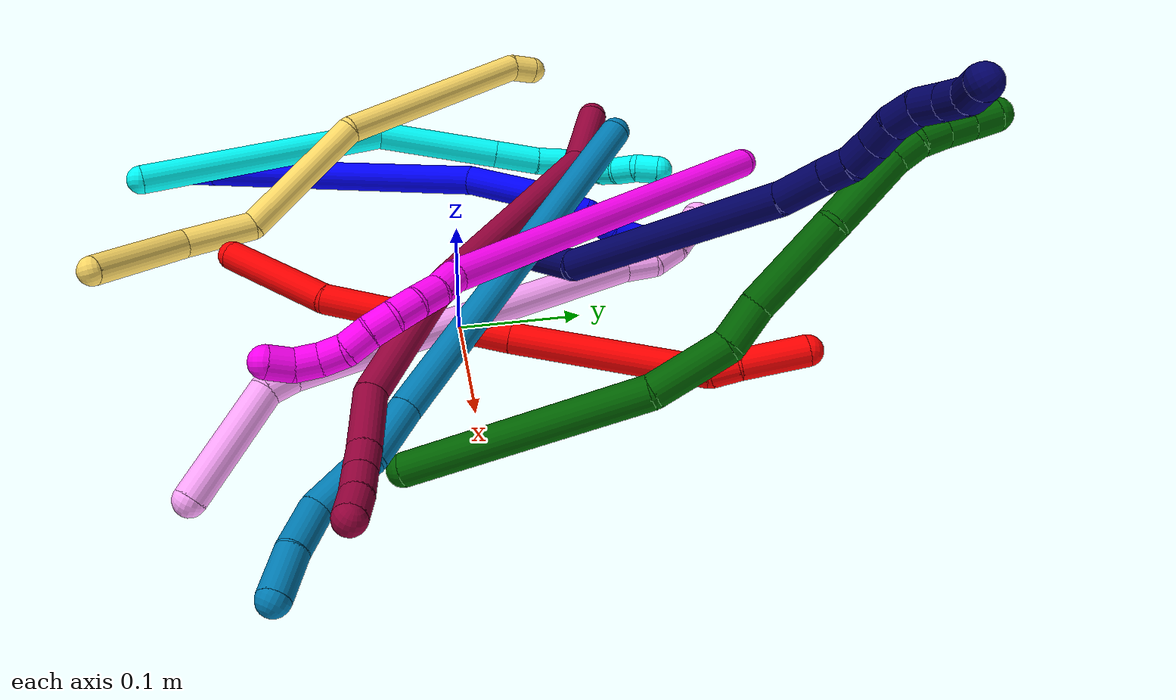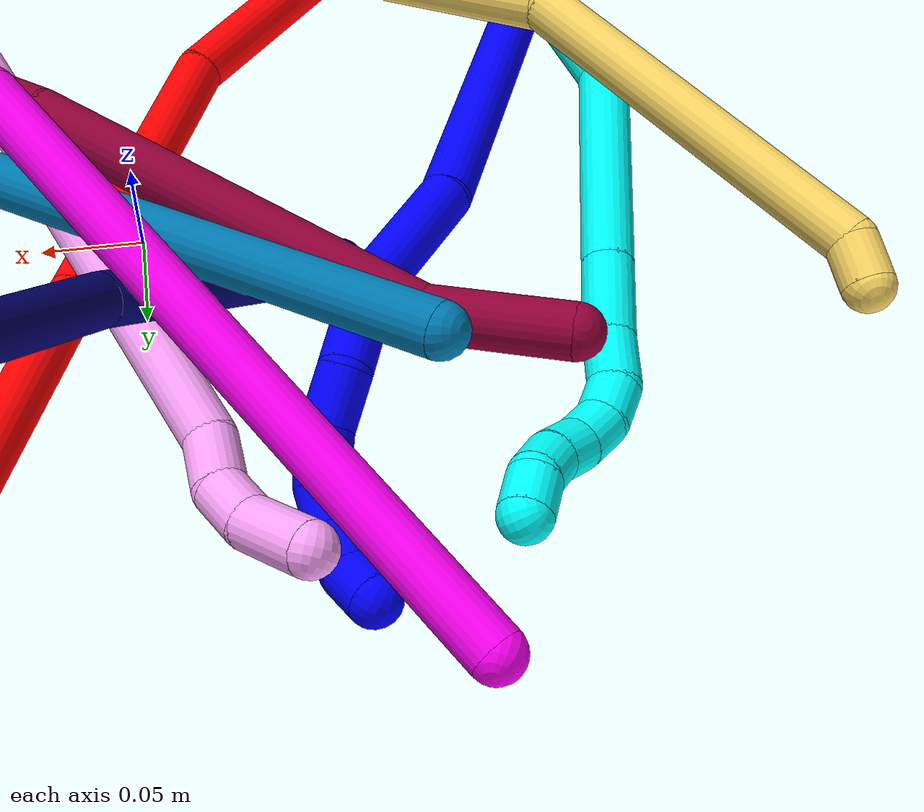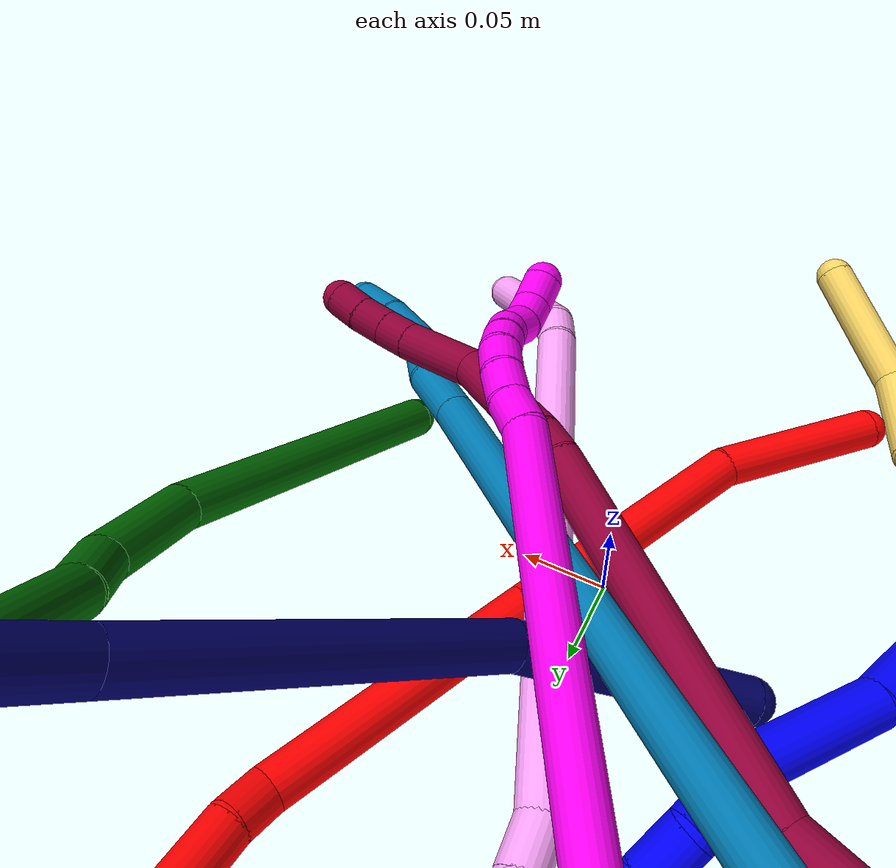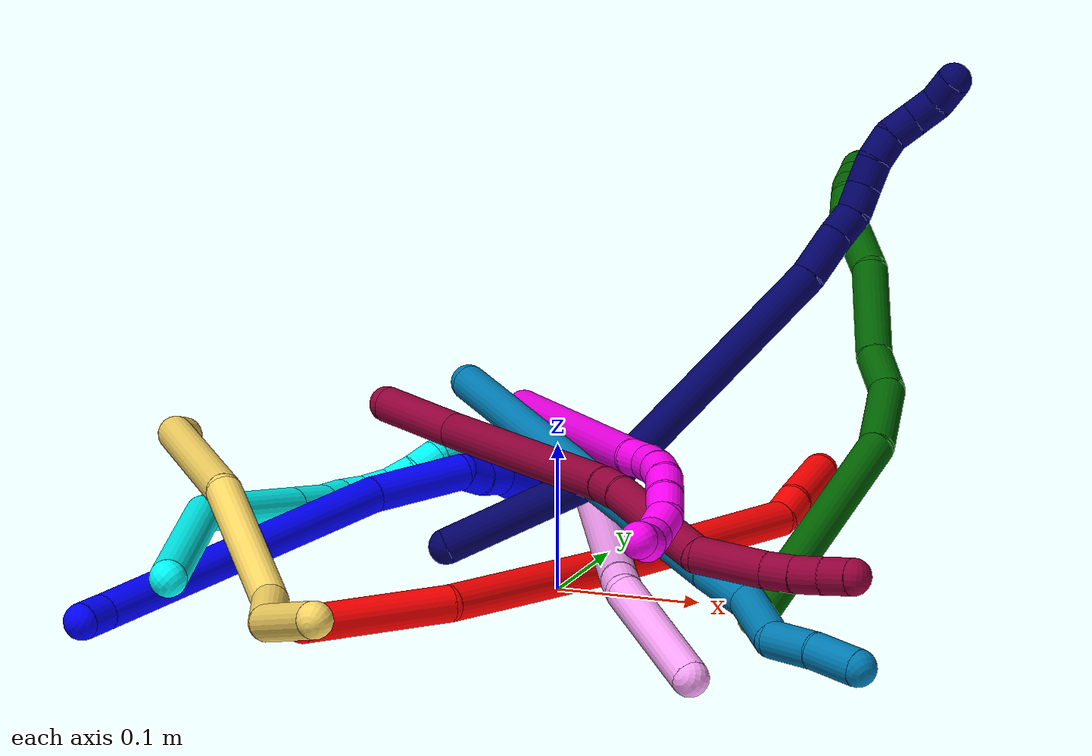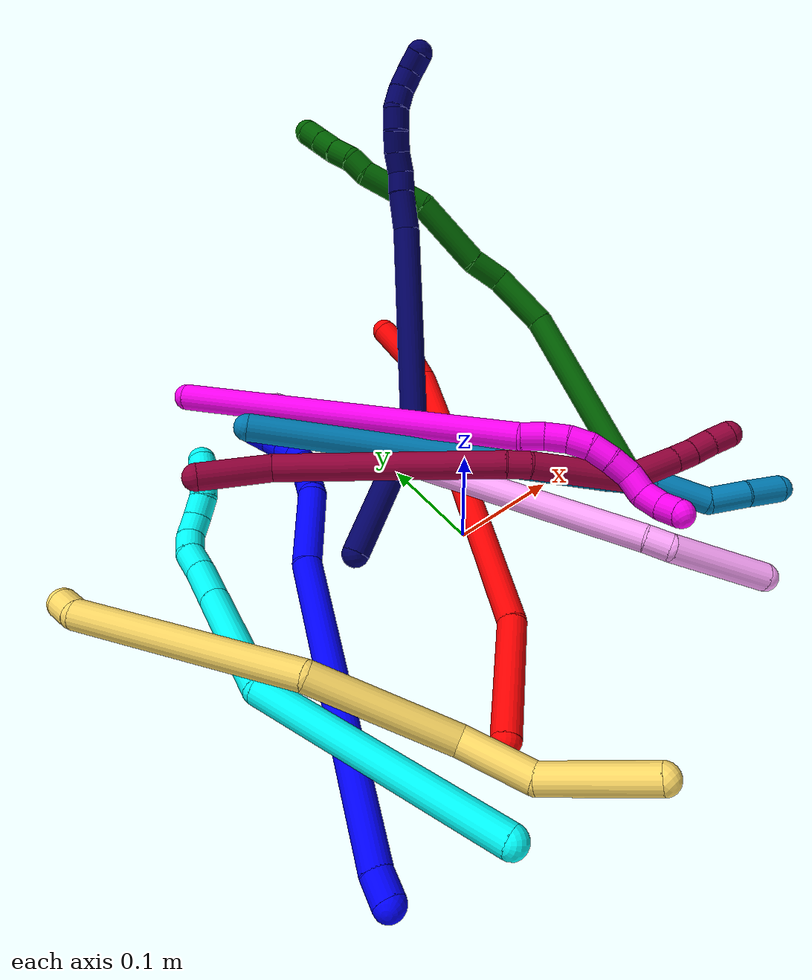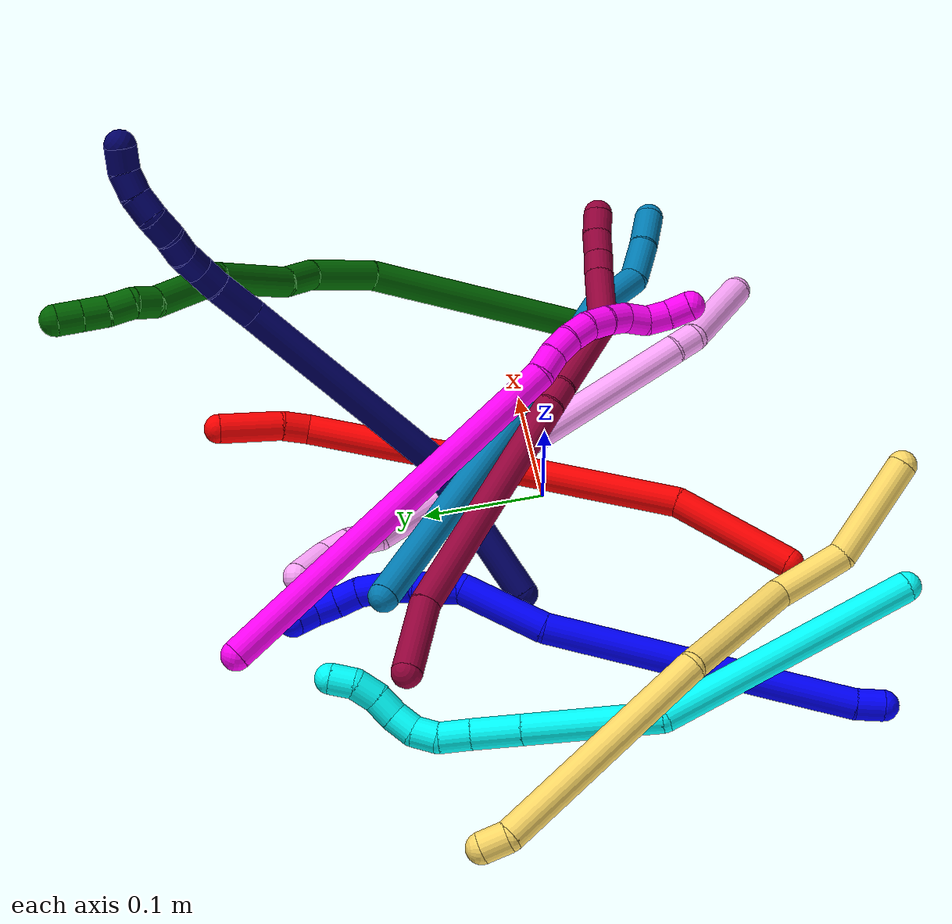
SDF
<sdf version="1.7">
 <world name="default">
  <plugin name="TubeGeneratorPlugin" filename="libtube_generator_plugin.so"/>
  <model name="photoneo_s_sensor">
   <static>1</static>
   <pose>0 0 2 1.57079 1.57079 3.14159</pose>
   <link name="link">
    <inertial><mass>0.1</mass></inertial>
    <sensor name="sensor" type="depth">
     <update_rate>30</update_rate>
     <camera>
      <horizontal_fov>1.22</horizontal_fov>
      <image><width>1920</width><height>1200</height><format>B8G8R8</format></image>
      <clip><near>0.1</near><far>2</far></clip>
      <depth_camera><output>points</output></depth_camera>
     </camera>
     <plugin name="camera_plugin" filename="libgazebo_ros_depth_camera.so">
      <baseline>0.2</baseline>
      <alwaysOn>1</alwaysOn>
      <updateRate>0.0</updateRate>
      <cameraName>camera_ir</cameraName>
      <imageTopicName>/camera/color/image_raw</imageTopicName>
      <cameraInfoTopicName>/camera/color/camera_info</cameraInfoTopicName>
      <depthImageTopicName>/camera/depth/image_raw</depthImageTopicName>
      <depthImageCameraInfoTopicName>/camera/depth/camera_info</depthImageCameraInfoTopicName>
      <pointCloudTopicName>/camera/depth/points</pointCloudTopicName>
      <frameName>fr_optical</frameName>
      <pointCloudCutoff>0.1</pointCloudCutoff>
      <pointCloudCutoffMax>2.0</pointCloudCutoffMax>
      <distortionK1>0</distortionK1>
      <distortionK2>0</distortionK2>
      <distortionK3>0</distortionK3>
      <distortionT1>0</distortionT1>
      <distortionT2>0</distortionT2>
      <CxPrime>0</CxPrime>
      <Cx>0</Cx>
      <Cy>0</Cy>
      <focalLength>0</focalLength>
      <hackBaseline>0</hackBaseline>
     </plugin>
    </sensor>
   </link>
  </model>
  <gravity>0 0 -9.8</gravity>
  <magnetic_field>6e-06 2.3e-05 -4.2e-05</magnetic_field>
  <atmosphere type="adiabatic"/>
  <physics name="default_physics" default="0" type="ode">
   <max_step_size>0.003</max_step_size>
   <real_time_factor>1</real_time_factor>
   <real_time_update_rate>1000</real_time_update_rate>
   <max_contacts>10000</max_contacts>
   <ode>
    <solver>
     <type>quick</type>
     <iters>100</iters>
     <sor>1.3</sor>
     <use_dynamic_moi_rescaling>0</use_dynamic_moi_rescaling>
    </solver>
    <constraints>
     <contact_max_correcting_vel>0</contact_max_correcting_vel>
     <contact_surface_layer>0.001</contact_surface_layer>
     <cfm>0</cfm>
     <erp>0.2</erp>
    </constraints>
   </ode>
  </physics>
  <scene><ambient>0.4 0.4 0.4 1</ambient><background>0.7 0.7 0.7 1</background><shadows>0</shadows></scene>
  <audio><device>default</device></audio>
  <spherical_coordinates>
   <surface_model>EARTH_WGS84</surface_model>
   <latitude_deg>0</latitude_deg>
   <longitude_deg>0</longitude_deg>
   <elevation>0</elevation>
   <heading_deg>0</heading_deg>
  </spherical_coordinates>
  <model name="bin">
   <static>1</static>
   <link name="bottom">
    <collision name="collision-bottom">
     <pose>0 0 -0.01 0 -0 0</pose>
     <geometry><box><size>0.8 0.6 0.02</size></box></geometry>
     <surface>
      <friction><ode><mu>100</mu><mu2>100</mu2></ode></friction>
      <contact><collide_bitmask>65535</collide_bitmask></contact>
     </surface>
    </collision>
   </link>
   <link name="west_wall">
    <collision name="collision-west_wall">
     <pose>-0.41 0 0.1 0 -0 0</pose>
     <geometry><box><size>0.02 0.6 0.2</size></box></geometry>
     <surface>
      <friction><ode><mu>100</mu><mu2>100</mu2></ode></friction>
      <contact><collide_bitmask>65535</collide_bitmask></contact>
     </surface>
    </collision>
   </link>
   <link name="east_wall">
    <collision name="collision-east_wall">
     <pose>0.41 0 0.1 0 -0 0</pose>
     <geometry><box><size>0.02 0.6 0.2</size></box></geometry>
     <surface>
      <friction><ode><mu>100</mu><mu2>100</mu2></ode></friction>
      <contact><collide_bitmask>65535</collide_bitmask></contact>
     </surface>
    </collision>
   </link>
   <link name="south_wall">
    <collision name="collision-south_wall">
     <pose>0 -0.31 0.1 0 -0 0</pose>
     <geometry><box><size>0.8 0.02 0.2</size></box></geometry>
     <surface>
      <friction><ode><mu>100</mu><mu2>100</mu2></ode></friction>
      <contact><collide_bitmask>65535</collide_bitmask></contact>
     </surface>
    </collision>
   </link>
   <link name="north_wall">
    <collision name="collision-north_wall">
     <pose>0 0.31 0.1 0 -0 0</pose>
     <geometry><box><size>0.8 0.02 0.2</size></box></geometry>
     <surface>
      <friction><ode><mu>100</mu><mu2>100</mu2></ode></friction>
      <contact><collide_bitmask>65535</collide_bitmask></contact>
     </surface>
    </collision>
   </link>
  </model>
  <model name="1">
   <static>0</static>
   <link name="1">
    <collision name="collision-cylinder-e_1_1_4">
     <pose>0.001003 0.008049 -0.007785 -2.33947 0.089374 -0.210129</pose>
     <geometry><cylinder><radius>0.0125</radius><length>0.022485</length></cylinder></geometry>
     <surface>
      <friction><ode><mu>1.16</mu><mu2>1.16</mu2><slip1>0</slip1><slip2>0</slip2></ode></friction>
      <contact><ode><kp>1e+06</kp><kd>1</kd><max_vel>0</max_vel><min_depth>0.001</min_depth></ode></contact>
     </surface>
    </collision>
    <visual name="visual-cylinder-e_1_1_4">
     <pose>0.001003 0.008049 -0.007785 -2.33947 0.089374 -0.210129</pose>
     <geometry><cylinder><radius>0.0125</radius><length>0.022485</length></cylinder></geometry>
     <material><ambient>0 0 1 1</ambient></material>
    </visual>
    <collision name="collision-cylinder-e_2_4_5">
     <pose>0.036285 0.100154 -0.103478 -2.3786 0.274702 -0.663646</pose>
     <geometry><cylinder><radius>0.0125</radius><length>0.252732</length></cylinder></geometry>
     <surface>
      <friction><ode><mu>1.16</mu><mu2>1.16</mu2><slip1>0</slip1><slip2>0</slip2></ode></friction>
      <contact><ode><kp>1e+06</kp><kd>1</kd><max_vel>0</max_vel><min_depth>0.001</min_depth></ode></contact>
     </surface>
    </collision>
    <visual name="visual-cylinder-e_2_4_5">
     <pose>0.036285 0.100154 -0.103478 -2.3786 0.274702 -0.663646</pose>
     <geometry><cylinder><radius>0.0125</radius><length>0.252732</length></cylinder></geometry>
     <material><ambient>0 0 1 1</ambient></material>
    </visual>
    <collision name="collision-cylinder-e_3_5_6">
     <pose>0.085696 0.201375 -0.219219 -2.58896 0.433446 -1.32044</pose>
     <geometry><cylinder><radius>0.0125</radius><length>0.072062</length></cylinder></geometry>
     <surface>
      <friction><ode><mu>1.16</mu><mu2>1.16</mu2><slip1>0</slip1><slip2>0</slip2></ode></friction>
      <contact><ode><kp>1e+06</kp><kd>1</kd><max_vel>0</max_vel><min_depth>0.001</min_depth></ode></contact>
     </surface>
    </collision>
    <visual name="visual-cylinder-e_3_5_6">
     <pose>0.085696 0.201375 -0.219219 -2.58896 0.433446 -1.32044</pose>
     <geometry><cylinder><radius>0.0125</radius><length>0.072062</length></cylinder></geometry>
     <material><ambient>0 0 1 1</ambient></material>
    </visual>
    <collision name="collision-cylinder-e_4_6_7">
     <pose>0.100255 0.222174 -0.256366 -2.76964 -0.057348 0.302555</pose>
     <geometry><cylinder><radius>0.0125</radius><length>0.020032</length></cylinder></geometry>
     <surface>
      <friction><ode><mu>1.16</mu><mu2>1.16</mu2><slip1>0</slip1><slip2>0</slip2></ode></friction>
      <contact><ode><kp>1e+06</kp><kd>1</kd><max_vel>0</max_vel><min_depth>0.001</min_depth></ode></contact>
     </surface>
    </collision>
    <visual name="visual-cylinder-e_4_6_7">
     <pose>0.100255 0.222174 -0.256366 -2.76964 -0.057348 0.302555</pose>
     <geometry><cylinder><radius>0.0125</radius><length>0.020032</length></cylinder></geometry>
     <material><ambient>0 0 1 1</ambient></material>
    </visual>
    <collision name="collision-cylinder-e_5_7_8">
     <pose>0.100366 0.231091 -0.274157 -2.58419 0.06853 -0.238448</pose>
     <geometry><cylinder><radius>0.0125</radius><length>0.02002</length></cylinder></geometry>
     <surface>
      <friction><ode><mu>1.16</mu><mu2>1.16</mu2><slip1>0</slip1><slip2>0</slip2></ode></friction>
      <contact><ode><kp>1e+06</kp><kd>1</kd><max_vel>0</max_vel><min_depth>0.001</min_depth></ode></contact>
     </surface>
    </collision>
    <visual name="visual-cylinder-e_5_7_8">
     <pose>0.100366 0.231091 -0.274157 -2.58419 0.06853 -0.238448</pose>
     <geometry><cylinder><radius>0.0125</radius><length>0.02002</length></cylinder></geometry>
     <material><ambient>0 0 1 1</ambient></material>
    </visual>
    <collision name="collision-cylinder-e_6_8_9">
     <pose>0.099744 0.239997 -0.295843 -2.87391 -0.095146 0.679737</pose>
     <geometry><cylinder><radius>0.0125</radius><length>0.027522</length></cylinder></geometry>
     <surface>
      <friction><ode><mu>1.16</mu><mu2>1.16</mu2><slip1>0</slip1><slip2>0</slip2></ode></friction>
      <contact><ode><kp>1e+06</kp><kd>1</kd><max_vel>0</max_vel><min_depth>0.001</min_depth></ode></contact>
     </surface>
    </collision>
    <visual name="visual-cylinder-e_6_8_9">
     <pose>0.099744 0.239997 -0.295843 -2.87391 -0.095146 0.679737</pose>
     <geometry><cylinder><radius>0.0125</radius><length>0.027522</length></cylinder></geometry>
     <material><ambient>0 0 1 1</ambient></material>
    </visual>
    <collision name="collision-cylinder-e_7_9_10">
     <pose>0.096235 0.249585 -0.319526 -2.62379 -0.180749 0.659354</pose>
     <geometry><cylinder><radius>0.0125</radius><length>0.024503</length></cylinder></geometry>
     <surface>
      <friction><ode><mu>1.16</mu><mu2>1.16</mu2><slip1>0</slip1><slip2>0</slip2></ode></friction>
      <contact><ode><kp>1e+06</kp><kd>1</kd><max_vel>0</max_vel><min_depth>0.001</min_depth></ode></contact>
     </surface>
    </collision>
    <visual name="visual-cylinder-e_7_9_10">
     <pose>0.096235 0.249585 -0.319526 -2.62379 -0.180749 0.659354</pose>
     <geometry><cylinder><radius>0.0125</radius><length>0.024503</length></cylinder></geometry>
     <material><ambient>0 0 1 1</ambient></material>
    </visual>
    <collision name="collision-cylinder-e_8_10_11">
     <pose>0.090012 0.262607 -0.336295 -2.2994 -0.401946 0.853764</pose>
     <geometry><cylinder><radius>0.0125</radius><length>0.020552</length></cylinder></geometry>
     <surface>
      <friction><ode><mu>1.16</mu><mu2>1.16</mu2><slip1>0</slip1><slip2>0</slip2></ode></friction>
      <contact><ode><kp>1e+06</kp><kd>1</kd><max_vel>0</max_vel><min_depth>0.001</min_depth></ode></contact>
     </surface>
    </collision>
    <visual name="visual-cylinder-e_8_10_11">
     <pose>0.090012 0.262607 -0.336295 -2.2994 -0.401946 0.853764</pose>
     <geometry><cylinder><radius>0.0125</radius><length>0.020552</length></cylinder></geometry>
     <material><ambient>0 0 1 1</ambient></material>
    </visual>
    <collision name="collision-cylinder-e_9_11_12">
     <pose>0.082974 0.277478 -0.348086 -2.18351 -0.305957 0.577132</pose>
     <geometry><cylinder><radius>0.0125</radius><length>0.020038</length></cylinder></geometry>
     <surface>
      <friction><ode><mu>1.16</mu><mu2>1.16</mu2><slip1>0</slip1><slip2>0</slip2></ode></friction>
      <contact><ode><kp>1e+06</kp><kd>1</kd><max_vel>0</max_vel><min_depth>0.001</min_depth></ode></contact>
     </surface>
    </collision>
    <visual name="visual-cylinder-e_9_11_12">
     <pose>0.082974 0.277478 -0.348086 -2.18351 -0.305957 0.577132</pose>
     <geometry><cylinder><radius>0.0125</radius><length>0.020038</length></cylinder></geometry>
     <material><ambient>0 0 1 1</ambient></material>
    </visual>
    <collision name="collision-cylinder-e_10_12_2">
     <pose>0.077382 0.29492 -0.354696 -1.68621 -0.2597 0.291121</pose>
     <geometry><cylinder><radius>0.0125</radius><length>0.020053</length></cylinder></geometry>
     <surface>
      <friction><ode><mu>1.16</mu><mu2>1.16</mu2><slip1>0</slip1><slip2>0</slip2></ode></friction>
      <contact><ode><kp>1e+06</kp><kd>1</kd><max_vel>0</max_vel><min_depth>0.001</min_depth></ode></contact>
     </surface>
    </collision>
    <visual name="visual-cylinder-e_10_12_2">
     <pose>0.077382 0.29492 -0.354696 -1.68621 -0.2597 0.291121</pose>
     <geometry><cylinder><radius>0.0125</radius><length>0.020053</length></cylinder></geometry>
     <material><ambient>0 0 1 1</ambient></material>
    </visual>
    <collision name="collision-sphere-2">
     <pose>0.074807 0.304546 -0.355812 0 -0 0</pose>
     <geometry><sphere><radius>0.0125</radius></sphere></geometry>
     <surface>
      <friction><ode><mu>1.16</mu><mu2>1.16</mu2><slip1>0</slip1><slip2>0</slip2></ode></friction>
      <contact><ode><kp>1e+06</kp><kd>1</kd><max_vel>0</max_vel><min_depth>0.001</min_depth></ode></contact>
     </surface>
    </collision>
    <visual name="visual-sphere-2">
     <pose>0.074807 0.304546 -0.355812 0 -0 0</pose>
     <geometry><sphere><radius>0.0125</radius></sphere></geometry>
     <material><ambient>0 0 1 1</ambient></material>
    </visual>
    <collision name="collision-sphere-12">
     <pose>0.079957 0.285294 -0.35358 0 -0 0</pose>
     <geometry><sphere><radius>0.0125</radius></sphere></geometry>
     <surface>
      <friction><ode><mu>1.16</mu><mu2>1.16</mu2><slip1>0</slip1><slip2>0</slip2></ode></friction>
      <contact><ode><kp>1e+06</kp><kd>1</kd><max_vel>0</max_vel><min_depth>0.001</min_depth></ode></contact>
     </surface>
    </collision>
    <visual name="visual-sphere-12">
     <pose>0.079957 0.285294 -0.35358 0 -0 0</pose>
     <geometry><sphere><radius>0.0125</radius></sphere></geometry>
     <material><ambient>0 0 1 1</ambient></material>
    </visual>
    <collision name="collision-sphere-11">
     <pose>0.085992 0.269663 -0.342592 0 -0 0</pose>
     <geometry><sphere><radius>0.0125</radius></sphere></geometry>
     <surface>
      <friction><ode><mu>1.16</mu><mu2>1.16</mu2><slip1>0</slip1><slip2>0</slip2></ode></friction>
      <contact><ode><kp>1e+06</kp><kd>1</kd><max_vel>0</max_vel><min_depth>0.001</min_depth></ode></contact>
     </surface>
    </collision>
    <visual name="visual-sphere-11">
     <pose>0.085992 0.269663 -0.342592 0 -0 0</pose>
     <geometry><sphere><radius>0.0125</radius></sphere></geometry>
     <material><ambient>0 0 1 1</ambient></material>
    </visual>
    <collision name="collision-sphere-10">
     <pose>0.094032 0.255551 -0.329998 0 -0 0</pose>
     <geometry><sphere><radius>0.0125</radius></sphere></geometry>
     <surface>
      <friction><ode><mu>1.16</mu><mu2>1.16</mu2><slip1>0</slip1><slip2>0</slip2></ode></friction>
      <contact><ode><kp>1e+06</kp><kd>1</kd><max_vel>0</max_vel><min_depth>0.001</min_depth></ode></contact>
     </surface>
    </collision>
    <visual name="visual-sphere-10">
     <pose>0.094032 0.255551 -0.329998 0 -0 0</pose>
     <geometry><sphere><radius>0.0125</radius></sphere></geometry>
     <material><ambient>0 0 1 1</ambient></material>
    </visual>
    <collision name="collision-sphere-9">
     <pose>0.098437 0.24362 -0.309054 0 -0 0</pose>
     <geometry><sphere><radius>0.0125</radius></sphere></geometry>
     <surface>
      <friction><ode><mu>1.16</mu><mu2>1.16</mu2><slip1>0</slip1><slip2>0</slip2></ode></friction>
      <contact><ode><kp>1e+06</kp><kd>1</kd><max_vel>0</max_vel><min_depth>0.001</min_depth></ode></contact>
     </surface>
    </collision>
    <visual name="visual-sphere-9">
     <pose>0.098437 0.24362 -0.309054 0 -0 0</pose>
     <geometry><sphere><radius>0.0125</radius></sphere></geometry>
     <material><ambient>0 0 1 1</ambient></material>
    </visual>
    <collision name="collision-sphere-4">
     <pose>0.002007 0.016099 -0.015569 0 -0 0</pose>
     <geometry><sphere><radius>0.0125</radius></sphere></geometry>
     <surface>
      <friction><ode><mu>1.16</mu><mu2>1.16</mu2><slip1>0</slip1><slip2>0</slip2></ode></friction>
      <contact><ode><kp>1e+06</kp><kd>1</kd><max_vel>0</max_vel><min_depth>0.001</min_depth></ode></contact>
     </surface>
    </collision>
    <visual name="visual-sphere-4">
     <pose>0.002007 0.016099 -0.015569 0 -0 0</pose>
     <geometry><sphere><radius>0.0125</radius></sphere></geometry>
     <material><ambient>0 0 1 1</ambient></material>
    </visual>
    <collision name="collision-sphere-1">
     <geometry><sphere><radius>0.0125</radius></sphere></geometry>
     <surface>
      <friction><ode><mu>1.16</mu><mu2>1.16</mu2><slip1>0</slip1><slip2>0</slip2></ode></friction>
      <contact><ode><kp>1e+06</kp><kd>1</kd><max_vel>0</max_vel><min_depth>0.001</min_depth></ode></contact>
     </surface>
    </collision>
    <visual name="visual-sphere-1">
     <geometry><sphere><radius>0.0125</radius></sphere></geometry>
     <material><ambient>0 0 1 1</ambient></material>
    </visual>
    <collision name="collision-sphere-8">
     <pose>0.101052 0.236373 -0.282632 0 -0 0</pose>
     <geometry><sphere><radius>0.0125</radius></sphere></geometry>
     <surface>
      <friction><ode><mu>1.16</mu><mu2>1.16</mu2><slip1>0</slip1><slip2>0</slip2></ode></friction>
      <contact><ode><kp>1e+06</kp><kd>1</kd><max_vel>0</max_vel><min_depth>0.001</min_depth></ode></contact>
     </surface>
    </collision>
    <visual name="visual-sphere-8">
     <pose>0.101052 0.236373 -0.282632 0 -0 0</pose>
     <geometry><sphere><radius>0.0125</radius></sphere></geometry>
     <material><ambient>0 0 1 1</ambient></material>
    </visual>
    <collision name="collision-sphere-5">
     <pose>0.070563 0.18421 -0.191388 0 -0 0</pose>
     <geometry><sphere><radius>0.0125</radius></sphere></geometry>
     <surface>
      <friction><ode><mu>1.16</mu><mu2>1.16</mu2><slip1>0</slip1><slip2>0</slip2></ode></friction>
      <contact><ode><kp>1e+06</kp><kd>1</kd><max_vel>0</max_vel><min_depth>0.001</min_depth></ode></contact>
     </surface>
    </collision>
    <visual name="visual-sphere-5">
     <pose>0.070563 0.18421 -0.191388 0 -0 0</pose>
     <geometry><sphere><radius>0.0125</radius></sphere></geometry>
     <material><ambient>0 0 1 1</ambient></material>
    </visual>
    <collision name="collision-sphere-6">
     <pose>0.100829 0.21854 -0.24705 0 -0 0</pose>
     <geometry><sphere><radius>0.0125</radius></sphere></geometry>
     <surface>
      <friction><ode><mu>1.16</mu><mu2>1.16</mu2><slip1>0</slip1><slip2>0</slip2></ode></friction>
      <contact><ode><kp>1e+06</kp><kd>1</kd><max_vel>0</max_vel><min_depth>0.001</min_depth></ode></contact>
     </surface>
    </collision>
    <visual name="visual-sphere-6">
     <pose>0.100829 0.21854 -0.24705 0 -0 0</pose>
     <geometry><sphere><radius>0.0125</radius></sphere></geometry>
     <material><ambient>0 0 1 1</ambient></material>
    </visual>
    <collision name="collision-sphere-7">
     <pose>0.099681 0.225808 -0.265682 0 -0 0</pose>
     <geometry><sphere><radius>0.0125</radius></sphere></geometry>
     <surface>
      <friction><ode><mu>1.16</mu><mu2>1.16</mu2><slip1>0</slip1><slip2>0</slip2></ode></friction>
      <contact><ode><kp>1e+06</kp><kd>1</kd><max_vel>0</max_vel><min_depth>0.001</min_depth></ode></contact>
     </surface>
    </collision>
    <visual name="visual-sphere-7">
     <pose>0.099681 0.225808 -0.265682 0 -0 0</pose>
     <geometry><sphere><radius>0.0125</radius></sphere></geometry>
     <material><ambient>0 0 1 1</ambient></material>
    </visual>
    <inertial>
     <pose>0.059107 0.157348 -0.179439 0 -0 0</pose>
     <mass>0.5</mass>
     <inertia>
      <ixx>0.000225</ixx>
      <ixy>0</ixy>
      <ixz>0</ixz>
      <iyy>-0.001428</iyy>
      <iyz>0</iyz>
      <izz>-0.001333</izz>
     </inertia>
    </inertial>
   </link>
   <pose>-0.248974 -0.222295 0.011492 0.736165 -0.722366 -0.148345</pose>
  </model>
  <model name="2">
   <static>0</static>
   <link name="2">
    <collision name="collision-cylinder-e_1_1_4">
     <pose>0.034204 0.037457 -0.014176 -1.93259 0.70684 -0.981043</pose>
     <geometry><cylinder><radius>0.0125</radius><length>0.105336</length></cylinder></geometry>
     <surface>
      <friction><ode><mu>1.16</mu><mu2>1.16</mu2><slip1>0</slip1><slip2>0</slip2></ode></friction>
      <contact><ode><kp>1e+06</kp><kd>1</kd><max_vel>0</max_vel><min_depth>0.001</min_depth></ode></contact>
     </surface>
    </collision>
    <visual name="visual-cylinder-e_1_1_4">
     <pose>0.034204 0.037457 -0.014176 -1.93259 0.70684 -0.981043</pose>
     <geometry><cylinder><radius>0.0125</radius><length>0.105336</length></cylinder></geometry>
     <material><ambient>1 0 0 1</ambient></material>
    </visual>
    <collision name="collision-cylinder-e_2_4_5">
     <pose>0.10403 0.14619 -0.035238 -1.66712 0.4616 -0.506463</pose>
     <geometry><cylinder><radius>0.0125</radius><length>0.159957</length></cylinder></geometry>
     <surface>
      <friction><ode><mu>1.16</mu><mu2>1.16</mu2><slip1>0</slip1><slip2>0</slip2></ode></friction>
      <contact><ode><kp>1e+06</kp><kd>1</kd><max_vel>0</max_vel><min_depth>0.001</min_depth></ode></contact>
     </surface>
    </collision>
    <visual name="visual-cylinder-e_2_4_5">
     <pose>0.10403 0.14619 -0.035238 -1.66712 0.4616 -0.506463</pose>
     <geometry><cylinder><radius>0.0125</radius><length>0.159957</length></cylinder></geometry>
     <material><ambient>1 0 0 1</ambient></material>
    </visual>
    <collision name="collision-cylinder-e_3_5_6">
     <pose>0.174946 0.288223 -0.046283 -1.62949 0.462023 -0.488899</pose>
     <geometry><cylinder><radius>0.0125</radius><length>0.158361</length></cylinder></geometry>
     <surface>
      <friction><ode><mu>1.16</mu><mu2>1.16</mu2><slip1>0</slip1><slip2>0</slip2></ode></friction>
      <contact><ode><kp>1e+06</kp><kd>1</kd><max_vel>0</max_vel><min_depth>0.001</min_depth></ode></contact>
     </surface>
    </collision>
    <visual name="visual-cylinder-e_3_5_6">
     <pose>0.174946 0.288223 -0.046283 -1.62949 0.462023 -0.488899</pose>
     <geometry><cylinder><radius>0.0125</radius><length>0.158361</length></cylinder></geometry>
     <material><ambient>1 0 0 1</ambient></material>
    </visual>
    <collision name="collision-cylinder-e_4_6_7">
     <pose>0.215189 0.368475 -0.046138 -1.14538 0.443121 -0.288462</pose>
     <geometry><cylinder><radius>0.0125</radius><length>0.023079</length></cylinder></geometry>
     <surface>
      <friction><ode><mu>1.16</mu><mu2>1.16</mu2><slip1>0</slip1><slip2>0</slip2></ode></friction>
      <contact><ode><kp>1e+06</kp><kd>1</kd><max_vel>0</max_vel><min_depth>0.001</min_depth></ode></contact>
     </surface>
    </collision>
    <visual name="visual-cylinder-e_4_6_7">
     <pose>0.215189 0.368475 -0.046138 -1.14538 0.443121 -0.288462</pose>
     <geometry><cylinder><radius>0.0125</radius><length>0.023079</length></cylinder></geometry>
     <material><ambient>1 0 0 1</ambient></material>
    </visual>
    <collision name="collision-cylinder-e_5_7_2">
     <pose>0.226997 0.40228 -0.033387 -1.2363 0.260524 -0.185783</pose>
     <geometry><cylinder><radius>0.0125</radius><length>0.053267</length></cylinder></geometry>
     <surface>
      <friction><ode><mu>1.16</mu><mu2>1.16</mu2><slip1>0</slip1><slip2>0</slip2></ode></friction>
      <contact><ode><kp>1e+06</kp><kd>1</kd><max_vel>0</max_vel><min_depth>0.001</min_depth></ode></contact>
     </surface>
    </collision>
    <visual name="visual-cylinder-e_5_7_2">
     <pose>0.226997 0.40228 -0.033387 -1.2363 0.260524 -0.185783</pose>
     <geometry><cylinder><radius>0.0125</radius><length>0.053267</length></cylinder></geometry>
     <material><ambient>1 0 0 1</ambient></material>
    </visual>
    <collision name="collision-sphere-2">
     <pose>0.233858 0.426588 -0.024939 0 -0 0</pose>
     <geometry><sphere><radius>0.0125</radius></sphere></geometry>
     <surface>
      <friction><ode><mu>1.16</mu><mu2>1.16</mu2><slip1>0</slip1><slip2>0</slip2></ode></friction>
      <contact><ode><kp>1e+06</kp><kd>1</kd><max_vel>0</max_vel><min_depth>0.001</min_depth></ode></contact>
     </surface>
    </collision>
    <visual name="visual-sphere-2">
     <pose>0.233858 0.426588 -0.024939 0 -0 0</pose>
     <geometry><sphere><radius>0.0125</radius></sphere></geometry>
     <material><ambient>1 0 0 1</ambient></material>
    </visual>
    <collision name="collision-sphere-7">
     <pose>0.220137 0.377971 -0.041836 0 -0 0</pose>
     <geometry><sphere><radius>0.0125</radius></sphere></geometry>
     <surface>
      <friction><ode><mu>1.16</mu><mu2>1.16</mu2><slip1>0</slip1><slip2>0</slip2></ode></friction>
      <contact><ode><kp>1e+06</kp><kd>1</kd><max_vel>0</max_vel><min_depth>0.001</min_depth></ode></contact>
     </surface>
    </collision>
    <visual name="visual-sphere-7">
     <pose>0.220137 0.377971 -0.041836 0 -0 0</pose>
     <geometry><sphere><radius>0.0125</radius></sphere></geometry>
     <material><ambient>1 0 0 1</ambient></material>
    </visual>
    <collision name="collision-sphere-6">
     <pose>0.210241 0.358979 -0.050441 0 -0 0</pose>
     <geometry><sphere><radius>0.0125</radius></sphere></geometry>
     <surface>
      <friction><ode><mu>1.16</mu><mu2>1.16</mu2><slip1>0</slip1><slip2>0</slip2></ode></friction>
      <contact><ode><kp>1e+06</kp><kd>1</kd><max_vel>0</max_vel><min_depth>0.001</min_depth></ode></contact>
     </surface>
    </collision>
    <visual name="visual-sphere-6">
     <pose>0.210241 0.358979 -0.050441 0 -0 0</pose>
     <geometry><sphere><radius>0.0125</radius></sphere></geometry>
     <material><ambient>1 0 0 1</ambient></material>
    </visual>
    <collision name="collision-sphere-5">
     <pose>0.139651 0.217466 -0.042125 0 -0 0</pose>
     <geometry><sphere><radius>0.0125</radius></sphere></geometry>
     <surface>
      <friction><ode><mu>1.16</mu><mu2>1.16</mu2><slip1>0</slip1><slip2>0</slip2></ode></friction>
      <contact><ode><kp>1e+06</kp><kd>1</kd><max_vel>0</max_vel><min_depth>0.001</min_depth></ode></contact>
     </surface>
    </collision>
    <visual name="visual-sphere-5">
     <pose>0.139651 0.217466 -0.042125 0 -0 0</pose>
     <geometry><sphere><radius>0.0125</radius></sphere></geometry>
     <material><ambient>1 0 0 1</ambient></material>
    </visual>
    <collision name="collision-sphere-1">
     <geometry><sphere><radius>0.0125</radius></sphere></geometry>
     <surface>
      <friction><ode><mu>1.16</mu><mu2>1.16</mu2><slip1>0</slip1><slip2>0</slip2></ode></friction>
      <contact><ode><kp>1e+06</kp><kd>1</kd><max_vel>0</max_vel><min_depth>0.001</min_depth></ode></contact>
     </surface>
    </collision>
    <visual name="visual-sphere-1">
     <geometry><sphere><radius>0.0125</radius></sphere></geometry>
     <material><ambient>1 0 0 1</ambient></material>
    </visual>
    <collision name="collision-sphere-4">
     <pose>0.068409 0.074914 -0.028351 0 -0 0</pose>
     <geometry><sphere><radius>0.0125</radius></sphere></geometry>
     <surface>
      <friction><ode><mu>1.16</mu><mu2>1.16</mu2><slip1>0</slip1><slip2>0</slip2></ode></friction>
      <contact><ode><kp>1e+06</kp><kd>1</kd><max_vel>0</max_vel><min_depth>0.001</min_depth></ode></contact>
     </surface>
    </collision>
    <visual name="visual-sphere-4">
     <pose>0.068409 0.074914 -0.028351 0 -0 0</pose>
     <geometry><sphere><radius>0.0125</radius></sphere></geometry>
     <material><ambient>1 0 0 1</ambient></material>
    </visual>
    <inertial>
     <pose>0.130011 0.20581 -0.034605 0 -0 0</pose>
     <mass>0.5</mass>
     <inertia>
      <ixx>0.000255</ixx>
      <ixy>0</ixy>
      <ixz>0</ixz>
      <iyy>-0.00019</iyy>
      <iyz>0</iyz>
      <izz>-0.001075</izz>
     </inertia>
    </inertial>
   </link>
   <pose>-0.109432 -0.182395 0.012675 -0.327978 -0.660235 0.174605</pose>
  </model>
  <model name="3">
   <static>0</static>
   <link name="3">
    <collision name="collision-cylinder-e_1_1_4">
     <pose>-0.028188 0.102792 0.031234 -1.2758 -0.256599 0.190684</pose>
     <geometry><cylinder><radius>0.0125</radius><length>0.222138</length></cylinder></geometry>
     <surface>
      <friction><ode><mu>1.16</mu><mu2>1.16</mu2><slip1>0</slip1><slip2>0</slip2></ode></friction>
      <contact><ode><kp>1e+06</kp><kd>1</kd><max_vel>0</max_vel><min_depth>0.001</min_depth></ode></contact>
     </surface>
    </collision>
    <visual name="visual-cylinder-e_1_1_4">
     <pose>-0.028188 0.102792 0.031234 -1.2758 -0.256599 0.190684</pose>
     <geometry><cylinder><radius>0.0125</radius><length>0.222138</length></cylinder></geometry>
     <material><ambient>0.003922 1 0.996078 1</ambient></material>
    </visual>
    <collision name="collision-cylinder-e_2_4_5">
     <pose>-0.057815 0.260384 0.054405 -1.7169 -0.025951 0.030049</pose>
     <geometry><cylinder><radius>0.0125</radius><length>0.110819</length></cylinder></geometry>
     <surface>
      <friction><ode><mu>1.16</mu><mu2>1.16</mu2><slip1>0</slip1><slip2>0</slip2></ode></friction>
      <contact><ode><kp>1e+06</kp><kd>1</kd><max_vel>0</max_vel><min_depth>0.001</min_depth></ode></contact>
     </surface>
    </collision>
    <visual name="visual-cylinder-e_2_4_5">
     <pose>-0.057815 0.260384 0.054405 -1.7169 -0.025951 0.030049</pose>
     <geometry><cylinder><radius>0.0125</radius><length>0.110819</length></cylinder></geometry>
     <material><ambient>0.003922 1 0.996078 1</ambient></material>
    </visual>
    <collision name="collision-cylinder-e_3_5_6">
     <pose>-0.059786 0.33526 0.04338 -1.71725 -0.026272 0.030431</pose>
     <geometry><cylinder><radius>0.0125</radius><length>0.040598</length></cylinder></geometry>
     <surface>
      <friction><ode><mu>1.16</mu><mu2>1.16</mu2><slip1>0</slip1><slip2>0</slip2></ode></friction>
      <contact><ode><kp>1e+06</kp><kd>1</kd><max_vel>0</max_vel><min_depth>0.001</min_depth></ode></contact>
     </surface>
    </collision>
    <visual name="visual-cylinder-e_3_5_6">
     <pose>-0.059786 0.33526 0.04338 -1.71725 -0.026272 0.030431</pose>
     <geometry><cylinder><radius>0.0125</radius><length>0.040598</length></cylinder></geometry>
     <material><ambient>0.003922 1 0.996078 1</ambient></material>
    </visual>
    <collision name="collision-cylinder-e_4_6_7">
     <pose>-0.060317 0.368279 0.039908 -1.61021 0.000127 -0.000132</pose>
     <geometry><cylinder><radius>0.0125</radius><length>0.02591</length></cylinder></geometry>
     <surface>
      <friction><ode><mu>1.16</mu><mu2>1.16</mu2><slip1>0</slip1><slip2>0</slip2></ode></friction>
      <contact><ode><kp>1e+06</kp><kd>1</kd><max_vel>0</max_vel><min_depth>0.001</min_depth></ode></contact>
     </surface>
    </collision>
    <visual name="visual-cylinder-e_4_6_7">
     <pose>-0.060317 0.368279 0.039908 -1.61021 0.000127 -0.000132</pose>
     <geometry><cylinder><radius>0.0125</radius><length>0.02591</length></cylinder></geometry>
     <material><ambient>0.003922 1 0.996078 1</ambient></material>
    </visual>
    <collision name="collision-cylinder-e_5_7_8">
     <pose>-0.057572 0.390483 0.036314 -1.89222 0.274042 -0.377916</pose>
     <geometry><cylinder><radius>0.0125</radius><length>0.020274</length></cylinder></geometry>
     <surface>
      <friction><ode><mu>1.16</mu><mu2>1.16</mu2><slip1>0</slip1><slip2>0</slip2></ode></friction>
      <contact><ode><kp>1e+06</kp><kd>1</kd><max_vel>0</max_vel><min_depth>0.001</min_depth></ode></contact>
     </surface>
    </collision>
    <visual name="visual-cylinder-e_5_7_8">
     <pose>-0.057572 0.390483 0.036314 -1.89222 0.274042 -0.377916</pose>
     <geometry><cylinder><radius>0.0125</radius><length>0.020274</length></cylinder></geometry>
     <material><ambient>0.003922 1 0.996078 1</ambient></material>
    </visual>
    <collision name="collision-cylinder-e_6_8_9">
     <pose>-0.048842 0.406847 0.029526 -2.05155 0.641674 -1.00282</pose>
     <geometry><cylinder><radius>0.0125</radius><length>0.020007</length></cylinder></geometry>
     <surface>
      <friction><ode><mu>1.16</mu><mu2>1.16</mu2><slip1>0</slip1><slip2>0</slip2></ode></friction>
      <contact><ode><kp>1e+06</kp><kd>1</kd><max_vel>0</max_vel><min_depth>0.001</min_depth></ode></contact>
     </surface>
    </collision>
    <visual name="visual-cylinder-e_6_8_9">
     <pose>-0.048842 0.406847 0.029526 -2.05155 0.641674 -1.00282</pose>
     <geometry><cylinder><radius>0.0125</radius><length>0.020007</length></cylinder></geometry>
     <material><ambient>0.003922 1 0.996078 1</ambient></material>
    </visual>
    <collision name="collision-cylinder-e_7_9_10">
     <pose>-0.035008 0.419809 0.023713 -1.91608 0.90022 -1.2043</pose>
     <geometry><cylinder><radius>0.0125</radius><length>0.020031</length></cylinder></geometry>
     <surface>
      <friction><ode><mu>1.16</mu><mu2>1.16</mu2><slip1>0</slip1><slip2>0</slip2></ode></friction>
      <contact><ode><kp>1e+06</kp><kd>1</kd><max_vel>0</max_vel><min_depth>0.001</min_depth></ode></contact>
     </surface>
    </collision>
    <visual name="visual-cylinder-e_7_9_10">
     <pose>-0.035008 0.419809 0.023713 -1.91608 0.90022 -1.2043</pose>
     <geometry><cylinder><radius>0.0125</radius><length>0.020031</length></cylinder></geometry>
     <material><ambient>0.003922 1 0.996078 1</ambient></material>
    </visual>
    <collision name="collision-cylinder-e_8_10_11">
     <pose>-0.020496 0.433219 0.020922 -1.66115 0.720953 -0.782713</pose>
     <geometry><cylinder><radius>0.0125</radius><length>0.020195</length></cylinder></geometry>
     <surface>
      <friction><ode><mu>1.16</mu><mu2>1.16</mu2><slip1>0</slip1><slip2>0</slip2></ode></friction>
      <contact><ode><kp>1e+06</kp><kd>1</kd><max_vel>0</max_vel><min_depth>0.001</min_depth></ode></contact>
     </surface>
    </collision>
    <visual name="visual-cylinder-e_8_10_11">
     <pose>-0.020496 0.433219 0.020922 -1.66115 0.720953 -0.782713</pose>
     <geometry><cylinder><radius>0.0125</radius><length>0.020195</length></cylinder></geometry>
     <material><ambient>0.003922 1 0.996078 1</ambient></material>
    </visual>
    <collision name="collision-cylinder-e_9_11_2">
     <pose>-0.011015 0.450254 0.018659 -1.7358 0.284949 -0.335436</pose>
     <geometry><cylinder><radius>0.0125</radius><length>0.02003</length></cylinder></geometry>
     <surface>
      <friction><ode><mu>1.16</mu><mu2>1.16</mu2><slip1>0</slip1><slip2>0</slip2></ode></friction>
      <contact><ode><kp>1e+06</kp><kd>1</kd><max_vel>0</max_vel><min_depth>0.001</min_depth></ode></contact>
     </surface>
    </collision>
    <visual name="visual-cylinder-e_9_11_2">
     <pose>-0.011015 0.450254 0.018659 -1.7358 0.284949 -0.335436</pose>
     <geometry><cylinder><radius>0.0125</radius><length>0.02003</length></cylinder></geometry>
     <material><ambient>0.003922 1 0.996078 1</ambient></material>
    </visual>
    <collision name="collision-sphere-2">
     <pose>-0.0082 0.459734 0.017081 0 -0 0</pose>
     <geometry><sphere><radius>0.0125</radius></sphere></geometry>
     <surface>
      <friction><ode><mu>1.16</mu><mu2>1.16</mu2><slip1>0</slip1><slip2>0</slip2></ode></friction>
      <contact><ode><kp>1e+06</kp><kd>1</kd><max_vel>0</max_vel><min_depth>0.001</min_depth></ode></contact>
     </surface>
    </collision>
    <visual name="visual-sphere-2">
     <pose>-0.0082 0.459734 0.017081 0 -0 0</pose>
     <geometry><sphere><radius>0.0125</radius></sphere></geometry>
     <material><ambient>0.003922 1 0.996078 1</ambient></material>
    </visual>
    <collision name="collision-sphere-11">
     <pose>-0.013831 0.440773 0.020238 0 -0 0</pose>
     <geometry><sphere><radius>0.0125</radius></sphere></geometry>
     <surface>
      <friction><ode><mu>1.16</mu><mu2>1.16</mu2><slip1>0</slip1><slip2>0</slip2></ode></friction>
      <contact><ode><kp>1e+06</kp><kd>1</kd><max_vel>0</max_vel><min_depth>0.001</min_depth></ode></contact>
     </surface>
    </collision>
    <visual name="visual-sphere-11">
     <pose>-0.013831 0.440773 0.020238 0 -0 0</pose>
     <geometry><sphere><radius>0.0125</radius></sphere></geometry>
     <material><ambient>0.003922 1 0.996078 1</ambient></material>
    </visual>
    <collision name="collision-sphere-10">
     <pose>-0.027161 0.425665 0.021607 0 -0 0</pose>
     <geometry><sphere><radius>0.0125</radius></sphere></geometry>
     <surface>
      <friction><ode><mu>1.16</mu><mu2>1.16</mu2><slip1>0</slip1><slip2>0</slip2></ode></friction>
      <contact><ode><kp>1e+06</kp><kd>1</kd><max_vel>0</max_vel><min_depth>0.001</min_depth></ode></contact>
     </surface>
    </collision>
    <visual name="visual-sphere-10">
     <pose>-0.027161 0.425665 0.021607 0 -0 0</pose>
     <geometry><sphere><radius>0.0125</radius></sphere></geometry>
     <material><ambient>0.003922 1 0.996078 1</ambient></material>
    </visual>
    <collision name="collision-sphere-9">
     <pose>-0.042854 0.413952 0.02582 0 -0 0</pose>
     <geometry><sphere><radius>0.0125</radius></sphere></geometry>
     <surface>
      <friction><ode><mu>1.16</mu><mu2>1.16</mu2><slip1>0</slip1><slip2>0</slip2></ode></friction>
      <contact><ode><kp>1e+06</kp><kd>1</kd><max_vel>0</max_vel><min_depth>0.001</min_depth></ode></contact>
     </surface>
    </collision>
    <visual name="visual-sphere-9">
     <pose>-0.042854 0.413952 0.02582 0 -0 0</pose>
     <geometry><sphere><radius>0.0125</radius></sphere></geometry>
     <material><ambient>0.003922 1 0.996078 1</ambient></material>
    </visual>
    <collision name="collision-sphere-4">
     <pose>-0.056377 0.205583 0.062469 0 -0 0</pose>
     <geometry><sphere><radius>0.0125</radius></sphere></geometry>
     <surface>
      <friction><ode><mu>1.16</mu><mu2>1.16</mu2><slip1>0</slip1><slip2>0</slip2></ode></friction>
      <contact><ode><kp>1e+06</kp><kd>1</kd><max_vel>0</max_vel><min_depth>0.001</min_depth></ode></contact>
     </surface>
    </collision>
    <visual name="visual-sphere-4">
     <pose>-0.056377 0.205583 0.062469 0 -0 0</pose>
     <geometry><sphere><radius>0.0125</radius></sphere></geometry>
     <material><ambient>0.003922 1 0.996078 1</ambient></material>
    </visual>
    <collision name="collision-sphere-1">
     <geometry><sphere><radius>0.0125</radius></sphere></geometry>
     <surface>
      <friction><ode><mu>1.16</mu><mu2>1.16</mu2><slip1>0</slip1><slip2>0</slip2></ode></friction>
      <contact><ode><kp>1e+06</kp><kd>1</kd><max_vel>0</max_vel><min_depth>0.001</min_depth></ode></contact>
     </surface>
    </collision>
    <visual name="visual-sphere-1">
     <geometry><sphere><radius>0.0125</radius></sphere></geometry>
     <material><ambient>0.003922 1 0.996078 1</ambient></material>
    </visual>
    <collision name="collision-sphere-8">
     <pose>-0.054829 0.399742 0.033232 0 -0 0</pose>
     <geometry><sphere><radius>0.0125</radius></sphere></geometry>
     <surface>
      <friction><ode><mu>1.16</mu><mu2>1.16</mu2><slip1>0</slip1><slip2>0</slip2></ode></friction>
      <contact><ode><kp>1e+06</kp><kd>1</kd><max_vel>0</max_vel><min_depth>0.001</min_depth></ode></contact>
     </surface>
    </collision>
    <visual name="visual-sphere-8">
     <pose>-0.054829 0.399742 0.033232 0 -0 0</pose>
     <geometry><sphere><radius>0.0125</radius></sphere></geometry>
     <material><ambient>0.003922 1 0.996078 1</ambient></material>
    </visual>
    <collision name="collision-sphere-5">
     <pose>-0.059252 0.315185 0.046341 0 -0 0</pose>
     <geometry><sphere><radius>0.0125</radius></sphere></geometry>
     <surface>
      <friction><ode><mu>1.16</mu><mu2>1.16</mu2><slip1>0</slip1><slip2>0</slip2></ode></friction>
      <contact><ode><kp>1e+06</kp><kd>1</kd><max_vel>0</max_vel><min_depth>0.001</min_depth></ode></contact>
     </surface>
    </collision>
    <visual name="visual-sphere-5">
     <pose>-0.059252 0.315185 0.046341 0 -0 0</pose>
     <geometry><sphere><radius>0.0125</radius></sphere></geometry>
     <material><ambient>0.003922 1 0.996078 1</ambient></material>
    </visual>
    <collision name="collision-sphere-6">
     <pose>-0.060319 0.355334 0.040418 0 -0 0</pose>
     <geometry><sphere><radius>0.0125</radius></sphere></geometry>
     <surface>
      <friction><ode><mu>1.16</mu><mu2>1.16</mu2><slip1>0</slip1><slip2>0</slip2></ode></friction>
      <contact><ode><kp>1e+06</kp><kd>1</kd><max_vel>0</max_vel><min_depth>0.001</min_depth></ode></contact>
     </surface>
    </collision>
    <visual name="visual-sphere-6">
     <pose>-0.060319 0.355334 0.040418 0 -0 0</pose>
     <geometry><sphere><radius>0.0125</radius></sphere></geometry>
     <material><ambient>0.003922 1 0.996078 1</ambient></material>
    </visual>
    <collision name="collision-sphere-7">
     <pose>-0.060316 0.381224 0.039397 0 -0 0</pose>
     <geometry><sphere><radius>0.0125</radius></sphere></geometry>
     <surface>
      <friction><ode><mu>1.16</mu><mu2>1.16</mu2><slip1>0</slip1><slip2>0</slip2></ode></friction>
      <contact><ode><kp>1e+06</kp><kd>1</kd><max_vel>0</max_vel><min_depth>0.001</min_depth></ode></contact>
     </surface>
    </collision>
    <visual name="visual-sphere-7">
     <pose>-0.060316 0.381224 0.039397 0 -0 0</pose>
     <geometry><sphere><radius>0.0125</radius></sphere></geometry>
     <material><ambient>0.003922 1 0.996078 1</ambient></material>
    </visual>
    <inertial>
     <pose>-0.040278 0.234149 0.036722 0 -0 0</pose>
     <mass>0.5</mass>
     <inertia>
      <ixx>0.001176</ixx>
      <ixy>0</ixy>
      <ixz>0</ixz>
      <iyy>0.000494</iyy>
      <iyz>0</iyz>
      <izz>-0.00075</izz>
     </inertia>
    </inertial>
   </link>
   <pose>-0.172352 -0.256324 0.056895 -0.092199 -0.874686 -0.015062</pose>
  </model>
  <model name="4">
   <static>0</static>
   <link name="4">
    <collision name="collision-cylinder-e_1_1_4">
     <pose>-0.020651 0.04115 0.00604 -1.42506 -0.460875 0.39995</pose>
     <geometry><cylinder><radius>0.0125</radius><length>0.092871</length></cylinder></geometry>
     <surface>
      <friction><ode><mu>1.16</mu><mu2>1.16</mu2><slip1>0</slip1><slip2>0</slip2></ode></friction>
      <contact><ode><kp>1e+06</kp><kd>1</kd><max_vel>0</max_vel><min_depth>0.001</min_depth></ode></contact>
     </surface>
    </collision>
    <visual name="visual-cylinder-e_1_1_4">
     <pose>-0.020651 0.04115 0.00604 -1.42506 -0.460875 0.39995</pose>
     <geometry><cylinder><radius>0.0125</radius><length>0.092871</length></cylinder></geometry>
     <material><ambient>1 0.65098 0.996078 1</ambient></material>
    </visual>
    <collision name="collision-cylinder-e_2_4_5">
     <pose>-0.044679 0.090656 0.018184 -0.939929 -0.315379 0.161179</pose>
     <geometry><cylinder><radius>0.0125</radius><length>0.021773</length></cylinder></geometry>
     <surface>
      <friction><ode><mu>1.16</mu><mu2>1.16</mu2><slip1>0</slip1><slip2>0</slip2></ode></friction>
      <contact><ode><kp>1e+06</kp><kd>1</kd><max_vel>0</max_vel><min_depth>0.001</min_depth></ode></contact>
     </surface>
    </collision>
    <visual name="visual-cylinder-e_2_4_5">
     <pose>-0.044679 0.090656 0.018184 -0.939929 -0.315379 0.161179</pose>
     <geometry><cylinder><radius>0.0125</radius><length>0.021773</length></cylinder></geometry>
     <material><ambient>1 0.65098 0.996078 1</ambient></material>
    </visual>
    <collision name="collision-cylinder-e_3_5_6">
     <pose>-0.076456 0.20484 0.125583 -0.807277 -0.191494 0.08199</pose>
     <geometry><cylinder><radius>0.0125</radius><length>0.298437</length></cylinder></geometry>
     <surface>
      <friction><ode><mu>1.16</mu><mu2>1.16</mu2><slip1>0</slip1><slip2>0</slip2></ode></friction>
      <contact><ode><kp>1e+06</kp><kd>1</kd><max_vel>0</max_vel><min_depth>0.001</min_depth></ode></contact>
     </surface>
    </collision>
    <visual name="visual-cylinder-e_3_5_6">
     <pose>-0.076456 0.20484 0.125583 -0.807277 -0.191494 0.08199</pose>
     <geometry><cylinder><radius>0.0125</radius><length>0.298437</length></cylinder></geometry>
     <material><ambient>1 0.65098 0.996078 1</ambient></material>
    </visual>
    <collision name="collision-cylinder-e_4_6_7">
     <pose>-0.109822 0.316883 0.237786 -0.517954 -0.376574 0.100875</pose>
     <geometry><cylinder><radius>0.0125</radius><length>0.027006</length></cylinder></geometry>
     <surface>
      <friction><ode><mu>1.16</mu><mu2>1.16</mu2><slip1>0</slip1><slip2>0</slip2></ode></friction>
      <contact><ode><kp>1e+06</kp><kd>1</kd><max_vel>0</max_vel><min_depth>0.001</min_depth></ode></contact>
     </surface>
    </collision>
    <visual name="visual-cylinder-e_4_6_7">
     <pose>-0.109822 0.316883 0.237786 -0.517954 -0.376574 0.100875</pose>
     <geometry><cylinder><radius>0.0125</radius><length>0.027006</length></cylinder></geometry>
     <material><ambient>1 0.65098 0.996078 1</ambient></material>
    </visual>
    <collision name="collision-cylinder-e_5_7_8">
     <pose>-0.119335 0.332202 0.25472 -0.986168 -0.394753 0.2141</pose>
     <geometry><cylinder><radius>0.0125</radius><length>0.023648</length></cylinder></geometry>
     <surface>
      <friction><ode><mu>1.16</mu><mu2>1.16</mu2><slip1>0</slip1><slip2>0</slip2></ode></friction>
      <contact><ode><kp>1e+06</kp><kd>1</kd><max_vel>0</max_vel><min_depth>0.001</min_depth></ode></contact>
     </surface>
    </collision>
    <visual name="visual-cylinder-e_5_7_8">
     <pose>-0.119335 0.332202 0.25472 -0.986168 -0.394753 0.2141</pose>
     <geometry><cylinder><radius>0.0125</radius><length>0.023648</length></cylinder></geometry>
     <material><ambient>1 0.65098 0.996078 1</ambient></material>
    </visual>
    <collision name="collision-cylinder-e_6_8_2">
     <pose>-0.132749 0.356675 0.264472 -1.33281 -0.510967 0.405177</pose>
     <geometry><cylinder><radius>0.0125</radius><length>0.036265</length></cylinder></geometry>
     <surface>
      <friction><ode><mu>1.16</mu><mu2>1.16</mu2><slip1>0</slip1><slip2>0</slip2></ode></friction>
      <contact><ode><kp>1e+06</kp><kd>1</kd><max_vel>0</max_vel><min_depth>0.001</min_depth></ode></contact>
     </surface>
    </collision>
    <visual name="visual-cylinder-e_6_8_2">
     <pose>-0.132749 0.356675 0.264472 -1.33281 -0.510967 0.405177</pose>
     <geometry><cylinder><radius>0.0125</radius><length>0.036265</length></cylinder></geometry>
     <material><ambient>1 0.65098 0.996078 1</ambient></material>
    </visual>
    <collision name="collision-sphere-2">
     <pose>-0.141616 0.372045 0.268201 0 -0 0</pose>
     <geometry><sphere><radius>0.0125</radius></sphere></geometry>
     <surface>
      <friction><ode><mu>1.16</mu><mu2>1.16</mu2><slip1>0</slip1><slip2>0</slip2></ode></friction>
      <contact><ode><kp>1e+06</kp><kd>1</kd><max_vel>0</max_vel><min_depth>0.001</min_depth></ode></contact>
     </surface>
    </collision>
    <visual name="visual-sphere-2">
     <pose>-0.141616 0.372045 0.268201 0 -0 0</pose>
     <geometry><sphere><radius>0.0125</radius></sphere></geometry>
     <material><ambient>1 0.65098 0.996078 1</ambient></material>
    </visual>
    <collision name="collision-sphere-4">
     <pose>-0.041303 0.082299 0.01208 0 -0 0</pose>
     <geometry><sphere><radius>0.0125</radius></sphere></geometry>
     <surface>
      <friction><ode><mu>1.16</mu><mu2>1.16</mu2><slip1>0</slip1><slip2>0</slip2></ode></friction>
      <contact><ode><kp>1e+06</kp><kd>1</kd><max_vel>0</max_vel><min_depth>0.001</min_depth></ode></contact>
     </surface>
    </collision>
    <visual name="visual-sphere-4">
     <pose>-0.041303 0.082299 0.01208 0 -0 0</pose>
     <geometry><sphere><radius>0.0125</radius></sphere></geometry>
     <material><ambient>1 0.65098 0.996078 1</ambient></material>
    </visual>
    <collision name="collision-sphere-1">
     <geometry><sphere><radius>0.0125</radius></sphere></geometry>
     <surface>
      <friction><ode><mu>1.16</mu><mu2>1.16</mu2><slip1>0</slip1><slip2>0</slip2></ode></friction>
      <contact><ode><kp>1e+06</kp><kd>1</kd><max_vel>0</max_vel><min_depth>0.001</min_depth></ode></contact>
     </surface>
    </collision>
    <visual name="visual-sphere-1">
     <geometry><sphere><radius>0.0125</radius></sphere></geometry>
     <material><ambient>1 0.65098 0.996078 1</ambient></material>
    </visual>
    <collision name="collision-sphere-8">
     <pose>-0.123882 0.341304 0.260744 0 -0 0</pose>
     <geometry><sphere><radius>0.0125</radius></sphere></geometry>
     <surface>
      <friction><ode><mu>1.16</mu><mu2>1.16</mu2><slip1>0</slip1><slip2>0</slip2></ode></friction>
      <contact><ode><kp>1e+06</kp><kd>1</kd><max_vel>0</max_vel><min_depth>0.001</min_depth></ode></contact>
     </surface>
    </collision>
    <visual name="visual-sphere-8">
     <pose>-0.123882 0.341304 0.260744 0 -0 0</pose>
     <geometry><sphere><radius>0.0125</radius></sphere></geometry>
     <material><ambient>1 0.65098 0.996078 1</ambient></material>
    </visual>
    <collision name="collision-sphere-5">
     <pose>-0.048056 0.099014 0.024289 0 -0 0</pose>
     <geometry><sphere><radius>0.0125</radius></sphere></geometry>
     <surface>
      <friction><ode><mu>1.16</mu><mu2>1.16</mu2><slip1>0</slip1><slip2>0</slip2></ode></friction>
      <contact><ode><kp>1e+06</kp><kd>1</kd><max_vel>0</max_vel><min_depth>0.001</min_depth></ode></contact>
     </surface>
    </collision>
    <visual name="visual-sphere-5">
     <pose>-0.048056 0.099014 0.024289 0 -0 0</pose>
     <geometry><sphere><radius>0.0125</radius></sphere></geometry>
     <material><ambient>1 0.65098 0.996078 1</ambient></material>
    </visual>
    <collision name="collision-sphere-6">
     <pose>-0.104856 0.310666 0.226876 0 -0 0</pose>
     <geometry><sphere><radius>0.0125</radius></sphere></geometry>
     <surface>
      <friction><ode><mu>1.16</mu><mu2>1.16</mu2><slip1>0</slip1><slip2>0</slip2></ode></friction>
      <contact><ode><kp>1e+06</kp><kd>1</kd><max_vel>0</max_vel><min_depth>0.001</min_depth></ode></contact>
     </surface>
    </collision>
    <visual name="visual-sphere-6">
     <pose>-0.104856 0.310666 0.226876 0 -0 0</pose>
     <geometry><sphere><radius>0.0125</radius></sphere></geometry>
     <material><ambient>1 0.65098 0.996078 1</ambient></material>
    </visual>
    <collision name="collision-sphere-7">
     <pose>-0.114787 0.3231 0.248696 0 -0 0</pose>
     <geometry><sphere><radius>0.0125</radius></sphere></geometry>
     <surface>
      <friction><ode><mu>1.16</mu><mu2>1.16</mu2><slip1>0</slip1><slip2>0</slip2></ode></friction>
      <contact><ode><kp>1e+06</kp><kd>1</kd><max_vel>0</max_vel><min_depth>0.001</min_depth></ode></contact>
     </surface>
    </collision>
    <visual name="visual-sphere-7">
     <pose>-0.114787 0.3231 0.248696 0 -0 0</pose>
     <geometry><sphere><radius>0.0125</radius></sphere></geometry>
     <material><ambient>1 0.65098 0.996078 1</ambient></material>
    </visual>
    <inertial>
     <pose>-0.07262 0.192552 0.120944 0 -0 0</pose>
     <mass>0.5</mass>
     <inertia>
      <ixx>0.002442</ixx>
      <ixy>0</ixy>
      <ixz>0</ixz>
      <iyy>0.001823</iyy>
      <iyz>0</iyz>
      <izz>-0.001169</izz>
     </inertia>
    </inertial>
   </link>
   <pose>0.166026 -0.208069 0.011805 3.06105 1.15179 -2.03544</pose>
  </model>
  <model name="5">
   <static>0</static>
   <link name="5">
    <collision name="collision-cylinder-e_1_1_4">
     <pose>-0.030523 0.015689 -0.030489 -2.66636 -0.727359 2.00818</pose>
     <geometry><cylinder><radius>0.0125</radius><length>0.091813</length></cylinder></geometry>
     <surface>
      <friction><ode><mu>1.16</mu><mu2>1.16</mu2><slip1>0</slip1><slip2>0</slip2></ode></friction>
      <contact><ode><kp>1e+06</kp><kd>1</kd><max_vel>0</max_vel><min_depth>0.001</min_depth></ode></contact>
     </surface>
    </collision>
    <visual name="visual-cylinder-e_1_1_4">
     <pose>-0.030523 0.015689 -0.030489 -2.66636 -0.727359 2.00818</pose>
     <geometry><cylinder><radius>0.0125</radius><length>0.091813</length></cylinder></geometry>
     <material><ambient>1 0.858824 0.4 1</ambient></material>
    </visual>
    <collision name="collision-cylinder-e_2_4_5">
     <pose>-0.072486 0.036542 -0.089845 -2.96455 -0.371942 2.26005</pose>
     <geometry><cylinder><radius>0.0125</radius><length>0.062954</length></cylinder></geometry>
     <surface>
      <friction><ode><mu>1.16</mu><mu2>1.16</mu2><slip1>0</slip1><slip2>0</slip2></ode></friction>
      <contact><ode><kp>1e+06</kp><kd>1</kd><max_vel>0</max_vel><min_depth>0.001</min_depth></ode></contact>
     </surface>
    </collision>
    <visual name="visual-cylinder-e_2_4_5">
     <pose>-0.072486 0.036542 -0.089845 -2.96455 -0.371942 2.26005</pose>
     <geometry><cylinder><radius>0.0125</radius><length>0.062954</length></cylinder></geometry>
     <material><ambient>1 0.858824 0.4 1</ambient></material>
    </visual>
    <collision name="collision-cylinder-e_3_5_6">
     <pose>-0.089489 0.078061 -0.169433 -2.51973 -0.088911 0.275109</pose>
     <geometry><cylinder><radius>0.0125</radius><length>0.125304</length></cylinder></geometry>
     <surface>
      <friction><ode><mu>1.16</mu><mu2>1.16</mu2><slip1>0</slip1><slip2>0</slip2></ode></friction>
      <contact><ode><kp>1e+06</kp><kd>1</kd><max_vel>0</max_vel><min_depth>0.001</min_depth></ode></contact>
     </surface>
    </collision>
    <visual name="visual-cylinder-e_3_5_6">
     <pose>-0.089489 0.078061 -0.169433 -2.51973 -0.088911 0.275109</pose>
     <geometry><cylinder><radius>0.0125</radius><length>0.125304</length></cylinder></geometry>
     <material><ambient>1 0.858824 0.4 1</ambient></material>
    </visual>
    <collision name="collision-cylinder-e_4_6_7">
     <pose>-0.1382 0.148323 -0.302323 -2.75021 -0.451915 1.7184</pose>
     <geometry><cylinder><radius>0.0125</radius><length>0.197616</length></cylinder></geometry>
     <surface>
      <friction><ode><mu>1.16</mu><mu2>1.16</mu2><slip1>0</slip1><slip2>0</slip2></ode></friction>
      <contact><ode><kp>1e+06</kp><kd>1</kd><max_vel>0</max_vel><min_depth>0.001</min_depth></ode></contact>
     </surface>
    </collision>
    <visual name="visual-cylinder-e_4_6_7">
     <pose>-0.1382 0.148323 -0.302323 -2.75021 -0.451915 1.7184</pose>
     <geometry><cylinder><radius>0.0125</radius><length>0.197616</length></cylinder></geometry>
     <material><ambient>1 0.858824 0.4 1</ambient></material>
    </visual>
    <collision name="collision-cylinder-e_5_7_2">
     <pose>-0.186238 0.180513 -0.394369 2.96938 -0.453686 -2.42583</pose>
     <geometry><cylinder><radius>0.0125</radius><length>0.022313</length></cylinder></geometry>
     <surface>
      <friction><ode><mu>1.16</mu><mu2>1.16</mu2><slip1>0</slip1><slip2>0</slip2></ode></friction>
      <contact><ode><kp>1e+06</kp><kd>1</kd><max_vel>0</max_vel><min_depth>0.001</min_depth></ode></contact>
     </surface>
    </collision>
    <visual name="visual-cylinder-e_5_7_2">
     <pose>-0.186238 0.180513 -0.394369 2.96938 -0.453686 -2.42583</pose>
     <geometry><cylinder><radius>0.0125</radius><length>0.022313</length></cylinder></geometry>
     <material><ambient>1 0.858824 0.4 1</ambient></material>
    </visual>
    <collision name="collision-sphere-2">
     <pose>-0.191128 0.178795 -0.404249 0 -0 0</pose>
     <geometry><sphere><radius>0.0125</radius></sphere></geometry>
     <surface>
      <friction><ode><mu>1.16</mu><mu2>1.16</mu2><slip1>0</slip1><slip2>0</slip2></ode></friction>
      <contact><ode><kp>1e+06</kp><kd>1</kd><max_vel>0</max_vel><min_depth>0.001</min_depth></ode></contact>
     </surface>
    </collision>
    <visual name="visual-sphere-2">
     <pose>-0.191128 0.178795 -0.404249 0 -0 0</pose>
     <geometry><sphere><radius>0.0125</radius></sphere></geometry>
     <material><ambient>1 0.858824 0.4 1</ambient></material>
    </visual>
    <collision name="collision-sphere-7">
     <pose>-0.181348 0.182232 -0.38449 0 -0 0</pose>
     <geometry><sphere><radius>0.0125</radius></sphere></geometry>
     <surface>
      <friction><ode><mu>1.16</mu><mu2>1.16</mu2><slip1>0</slip1><slip2>0</slip2></ode></friction>
      <contact><ode><kp>1e+06</kp><kd>1</kd><max_vel>0</max_vel><min_depth>0.001</min_depth></ode></contact>
     </surface>
    </collision>
    <visual name="visual-sphere-7">
     <pose>-0.181348 0.182232 -0.38449 0 -0 0</pose>
     <geometry><sphere><radius>0.0125</radius></sphere></geometry>
     <material><ambient>1 0.858824 0.4 1</ambient></material>
    </visual>
    <collision name="collision-sphere-6">
     <pose>-0.095052 0.114415 -0.220155 0 -0 0</pose>
     <geometry><sphere><radius>0.0125</radius></sphere></geometry>
     <surface>
      <friction><ode><mu>1.16</mu><mu2>1.16</mu2><slip1>0</slip1><slip2>0</slip2></ode></friction>
      <contact><ode><kp>1e+06</kp><kd>1</kd><max_vel>0</max_vel><min_depth>0.001</min_depth></ode></contact>
     </surface>
    </collision>
    <visual name="visual-sphere-6">
     <pose>-0.095052 0.114415 -0.220155 0 -0 0</pose>
     <geometry><sphere><radius>0.0125</radius></sphere></geometry>
     <material><ambient>1 0.858824 0.4 1</ambient></material>
    </visual>
    <collision name="collision-sphere-5">
     <pose>-0.083925 0.041707 -0.118711 0 -0 0</pose>
     <geometry><sphere><radius>0.0125</radius></sphere></geometry>
     <surface>
      <friction><ode><mu>1.16</mu><mu2>1.16</mu2><slip1>0</slip1><slip2>0</slip2></ode></friction>
      <contact><ode><kp>1e+06</kp><kd>1</kd><max_vel>0</max_vel><min_depth>0.001</min_depth></ode></contact>
     </surface>
    </collision>
    <visual name="visual-sphere-5">
     <pose>-0.083925 0.041707 -0.118711 0 -0 0</pose>
     <geometry><sphere><radius>0.0125</radius></sphere></geometry>
     <material><ambient>1 0.858824 0.4 1</ambient></material>
    </visual>
    <collision name="collision-sphere-1">
     <geometry><sphere><radius>0.0125</radius></sphere></geometry>
     <surface>
      <friction><ode><mu>1.16</mu><mu2>1.16</mu2><slip1>0</slip1><slip2>0</slip2></ode></friction>
      <contact><ode><kp>1e+06</kp><kd>1</kd><max_vel>0</max_vel><min_depth>0.001</min_depth></ode></contact>
     </surface>
    </collision>
    <visual name="visual-sphere-1">
     <geometry><sphere><radius>0.0125</radius></sphere></geometry>
     <material><ambient>1 0.858824 0.4 1</ambient></material>
    </visual>
    <collision name="collision-sphere-4">
     <pose>-0.061046 0.031378 -0.060979 0 -0 0</pose>
     <geometry><sphere><radius>0.0125</radius></sphere></geometry>
     <surface>
      <friction><ode><mu>1.16</mu><mu2>1.16</mu2><slip1>0</slip1><slip2>0</slip2></ode></friction>
      <contact><ode><kp>1e+06</kp><kd>1</kd><max_vel>0</max_vel><min_depth>0.001</min_depth></ode></contact>
     </surface>
    </collision>
    <visual name="visual-sphere-4">
     <pose>-0.061046 0.031378 -0.060979 0 -0 0</pose>
     <geometry><sphere><radius>0.0125</radius></sphere></geometry>
     <material><ambient>1 0.858824 0.4 1</ambient></material>
    </visual>
    <inertial>
     <pose>-0.10009 0.093722 -0.196459 0 -0 0</pose>
     <mass>0.5</mass>
     <inertia>
      <ixx>0.000711</ixx>
      <ixy>0</ixy>
      <ixz>0</ixz>
      <iyy>0.000828</iyy>
      <iyz>0</iyz>
      <izz>-2.6e-05</izz>
     </inertia>
    </inertial>
   </link>
   <pose>-0.05791 -0.288189 0.048771 1.94301 -1.01756 -0.288421</pose>
  </model>
  <model name="6">
   <static>0</static>
   <link name="6">
    <collision name="collision-cylinder-e_1_1_4">
     <pose>-0.006915 0.032627 0.087616 -0.35648 -0.073829 0.013306</pose>
     <geometry><cylinder><radius>0.0125</radius><length>0.187498</length></cylinder></geometry>
     <surface>
      <friction><ode><mu>1.16</mu><mu2>1.16</mu2><slip1>0</slip1><slip2>0</slip2></ode></friction>
      <contact><ode><kp>1e+06</kp><kd>1</kd><max_vel>0</max_vel><min_depth>0.001</min_depth></ode></contact>
     </surface>
    </collision>
    <visual name="visual-cylinder-e_1_1_4">
     <pose>-0.006915 0.032627 0.087616 -0.35648 -0.073829 0.013306</pose>
     <geometry><cylinder><radius>0.0125</radius><length>0.187498</length></cylinder></geometry>
     <material><ambient>0 0.392157 0.003922 1</ambient></material>
    </visual>
    <collision name="collision-cylinder-e_2_4_5">
     <pose>-0.007233 0.073655 0.202589 -0.297941 0.226572 -0.034147</pose>
     <geometry><cylinder><radius>0.0125</radius><length>0.058737</length></cylinder></geometry>
     <surface>
      <friction><ode><mu>1.16</mu><mu2>1.16</mu2><slip1>0</slip1><slip2>0</slip2></ode></friction>
      <contact><ode><kp>1e+06</kp><kd>1</kd><max_vel>0</max_vel><min_depth>0.001</min_depth></ode></contact>
     </surface>
    </collision>
    <visual name="visual-cylinder-e_2_4_5">
     <pose>-0.007233 0.073655 0.202589 -0.297941 0.226572 -0.034147</pose>
     <geometry><cylinder><radius>0.0125</radius><length>0.058737</length></cylinder></geometry>
     <material><ambient>0 0.392157 0.003922 1</ambient></material>
    </visual>
    <collision name="collision-cylinder-e_3_5_6">
     <pose>0.009273 0.086857 0.242494 -0.365443 0.635494 -0.121397</pose>
     <geometry><cylinder><radius>0.0125</radius><length>0.033388</length></cylinder></geometry>
     <surface>
      <friction><ode><mu>1.16</mu><mu2>1.16</mu2><slip1>0</slip1><slip2>0</slip2></ode></friction>
      <contact><ode><kp>1e+06</kp><kd>1</kd><max_vel>0</max_vel><min_depth>0.001</min_depth></ode></contact>
     </surface>
    </collision>
    <visual name="visual-cylinder-e_3_5_6">
     <pose>0.009273 0.086857 0.242494 -0.365443 0.635494 -0.121397</pose>
     <geometry><cylinder><radius>0.0125</radius><length>0.033388</length></cylinder></geometry>
     <material><ambient>0 0.392157 0.003922 1</ambient></material>
    </visual>
    <collision name="collision-cylinder-e_4_6_7">
     <pose>0.034375 0.108172 0.284465 -0.511434 0.423074 -0.112171</pose>
     <geometry><cylinder><radius>0.0125</radius><length>0.074007</length></cylinder></geometry>
     <surface>
      <friction><ode><mu>1.16</mu><mu2>1.16</mu2><slip1>0</slip1><slip2>0</slip2></ode></friction>
      <contact><ode><kp>1e+06</kp><kd>1</kd><max_vel>0</max_vel><min_depth>0.001</min_depth></ode></contact>
     </surface>
    </collision>
    <visual name="visual-cylinder-e_4_6_7">
     <pose>0.034375 0.108172 0.284465 -0.511434 0.423074 -0.112171</pose>
     <geometry><cylinder><radius>0.0125</radius><length>0.074007</length></cylinder></geometry>
     <material><ambient>0 0.392157 0.003922 1</ambient></material>
    </visual>
    <collision name="collision-cylinder-e_5_7_8">
     <pose>0.067405 0.129102 0.340825 -0.16251 0.578838 -0.048489</pose>
     <geometry><cylinder><radius>0.0125</radius><length>0.065215</length></cylinder></geometry>
     <surface>
      <friction><ode><mu>1.16</mu><mu2>1.16</mu2><slip1>0</slip1><slip2>0</slip2></ode></friction>
      <contact><ode><kp>1e+06</kp><kd>1</kd><max_vel>0</max_vel><min_depth>0.001</min_depth></ode></contact>
     </surface>
    </collision>
    <visual name="visual-cylinder-e_5_7_8">
     <pose>0.067405 0.129102 0.340825 -0.16251 0.578838 -0.048489</pose>
     <geometry><cylinder><radius>0.0125</radius><length>0.065215</length></cylinder></geometry>
     <material><ambient>0 0.392157 0.003922 1</ambient></material>
    </visual>
    <collision name="collision-cylinder-e_6_8_9">
     <pose>0.088393 0.136611 0.376823 -0.328801 0.317773 -0.053153</pose>
     <geometry><cylinder><radius>0.0125</radius><length>0.020161</length></cylinder></geometry>
     <surface>
      <friction><ode><mu>1.16</mu><mu2>1.16</mu2><slip1>0</slip1><slip2>0</slip2></ode></friction>
      <contact><ode><kp>1e+06</kp><kd>1</kd><max_vel>0</max_vel><min_depth>0.001</min_depth></ode></contact>
     </surface>
    </collision>
    <visual name="visual-cylinder-e_6_8_9">
     <pose>0.088393 0.136611 0.376823 -0.328801 0.317773 -0.053153</pose>
     <geometry><cylinder><radius>0.0125</radius><length>0.020161</length></cylinder></geometry>
     <material><ambient>0 0.392157 0.003922 1</ambient></material>
    </visual>
    <collision name="collision-cylinder-e_7_9_10">
     <pose>0.093902 0.13894 0.395992 0.075319 0.228732 0.008656</pose>
     <geometry><cylinder><radius>0.0125</radius><length>0.02081</length></cylinder></geometry>
     <surface>
      <friction><ode><mu>1.16</mu><mu2>1.16</mu2><slip1>0</slip1><slip2>0</slip2></ode></friction>
      <contact><ode><kp>1e+06</kp><kd>1</kd><max_vel>0</max_vel><min_depth>0.001</min_depth></ode></contact>
     </surface>
    </collision>
    <visual name="visual-cylinder-e_7_9_10">
     <pose>0.093902 0.13894 0.395992 0.075319 0.228732 0.008656</pose>
     <geometry><cylinder><radius>0.0125</radius><length>0.02081</length></cylinder></geometry>
     <material><ambient>0 0.392157 0.003922 1</ambient></material>
    </visual>
    <collision name="collision-cylinder-e_8_10_11">
     <pose>0.097466 0.138239 0.416098 -0.006146 0.119862 -0.000369</pose>
     <geometry><cylinder><radius>0.0125</radius><length>0.020148</length></cylinder></geometry>
     <surface>
      <friction><ode><mu>1.16</mu><mu2>1.16</mu2><slip1>0</slip1><slip2>0</slip2></ode></friction>
      <contact><ode><kp>1e+06</kp><kd>1</kd><max_vel>0</max_vel><min_depth>0.001</min_depth></ode></contact>
     </surface>
    </collision>
    <visual name="visual-cylinder-e_8_10_11">
     <pose>0.097466 0.138239 0.416098 -0.006146 0.119862 -0.000369</pose>
     <geometry><cylinder><radius>0.0125</radius><length>0.020148</length></cylinder></geometry>
     <material><ambient>0 0.392157 0.003922 1</ambient></material>
    </visual>
    <collision name="collision-cylinder-e_9_11_2">
     <pose>0.099881 0.138403 0.436044 -0.010292 0.121112 -0.000624</pose>
     <geometry><cylinder><radius>0.0125</radius><length>0.020036</length></cylinder></geometry>
     <surface>
      <friction><ode><mu>1.16</mu><mu2>1.16</mu2><slip1>0</slip1><slip2>0</slip2></ode></friction>
      <contact><ode><kp>1e+06</kp><kd>1</kd><max_vel>0</max_vel><min_depth>0.001</min_depth></ode></contact>
     </surface>
    </collision>
    <visual name="visual-cylinder-e_9_11_2">
     <pose>0.099881 0.138403 0.436044 -0.010292 0.121112 -0.000624</pose>
     <geometry><cylinder><radius>0.0125</radius><length>0.020036</length></cylinder></geometry>
     <material><ambient>0 0.392157 0.003922 1</ambient></material>
    </visual>
    <collision name="collision-sphere-2">
     <pose>0.101091 0.138505 0.445988 0 -0 0</pose>
     <geometry><sphere><radius>0.0125</radius></sphere></geometry>
     <surface>
      <friction><ode><mu>1.16</mu><mu2>1.16</mu2><slip1>0</slip1><slip2>0</slip2></ode></friction>
      <contact><ode><kp>1e+06</kp><kd>1</kd><max_vel>0</max_vel><min_depth>0.001</min_depth></ode></contact>
     </surface>
    </collision>
    <visual name="visual-sphere-2">
     <pose>0.101091 0.138505 0.445988 0 -0 0</pose>
     <geometry><sphere><radius>0.0125</radius></sphere></geometry>
     <material><ambient>0 0.392157 0.003922 1</ambient></material>
    </visual>
    <collision name="collision-sphere-11">
     <pose>0.09867 0.138301 0.4261 0 -0 0</pose>
     <geometry><sphere><radius>0.0125</radius></sphere></geometry>
     <surface>
      <friction><ode><mu>1.16</mu><mu2>1.16</mu2><slip1>0</slip1><slip2>0</slip2></ode></friction>
      <contact><ode><kp>1e+06</kp><kd>1</kd><max_vel>0</max_vel><min_depth>0.001</min_depth></ode></contact>
     </surface>
    </collision>
    <visual name="visual-sphere-11">
     <pose>0.09867 0.138301 0.4261 0 -0 0</pose>
     <geometry><sphere><radius>0.0125</radius></sphere></geometry>
     <material><ambient>0 0.392157 0.003922 1</ambient></material>
    </visual>
    <collision name="collision-sphere-10">
     <pose>0.096261 0.138178 0.406097 0 -0 0</pose>
     <geometry><sphere><radius>0.0125</radius></sphere></geometry>
     <surface>
      <friction><ode><mu>1.16</mu><mu2>1.16</mu2><slip1>0</slip1><slip2>0</slip2></ode></friction>
      <contact><ode><kp>1e+06</kp><kd>1</kd><max_vel>0</max_vel><min_depth>0.001</min_depth></ode></contact>
     </surface>
    </collision>
    <visual name="visual-sphere-10">
     <pose>0.096261 0.138178 0.406097 0 -0 0</pose>
     <geometry><sphere><radius>0.0125</radius></sphere></geometry>
     <material><ambient>0 0.392157 0.003922 1</ambient></material>
    </visual>
    <collision name="collision-sphere-9">
     <pose>0.091542 0.139703 0.385886 0 -0 0</pose>
     <geometry><sphere><radius>0.0125</radius></sphere></geometry>
     <surface>
      <friction><ode><mu>1.16</mu><mu2>1.16</mu2><slip1>0</slip1><slip2>0</slip2></ode></friction>
      <contact><ode><kp>1e+06</kp><kd>1</kd><max_vel>0</max_vel><min_depth>0.001</min_depth></ode></contact>
     </surface>
    </collision>
    <visual name="visual-sphere-9">
     <pose>0.091542 0.139703 0.385886 0 -0 0</pose>
     <geometry><sphere><radius>0.0125</radius></sphere></geometry>
     <material><ambient>0 0.392157 0.003922 1</ambient></material>
    </visual>
    <collision name="collision-sphere-4">
     <pose>-0.01383 0.065254 0.175232 0 -0 0</pose>
     <geometry><sphere><radius>0.0125</radius></sphere></geometry>
     <surface>
      <friction><ode><mu>1.16</mu><mu2>1.16</mu2><slip1>0</slip1><slip2>0</slip2></ode></friction>
      <contact><ode><kp>1e+06</kp><kd>1</kd><max_vel>0</max_vel><min_depth>0.001</min_depth></ode></contact>
     </surface>
    </collision>
    <visual name="visual-sphere-4">
     <pose>-0.01383 0.065254 0.175232 0 -0 0</pose>
     <geometry><sphere><radius>0.0125</radius></sphere></geometry>
     <material><ambient>0 0.392157 0.003922 1</ambient></material>
    </visual>
    <collision name="collision-sphere-1">
     <geometry><sphere><radius>0.0125</radius></sphere></geometry>
     <surface>
      <friction><ode><mu>1.16</mu><mu2>1.16</mu2><slip1>0</slip1><slip2>0</slip2></ode></friction>
      <contact><ode><kp>1e+06</kp><kd>1</kd><max_vel>0</max_vel><min_depth>0.001</min_depth></ode></contact>
     </surface>
    </collision>
    <visual name="visual-sphere-1">
     <geometry><sphere><radius>0.0125</radius></sphere></geometry>
     <material><ambient>0 0.392157 0.003922 1</ambient></material>
    </visual>
    <collision name="collision-sphere-8">
     <pose>0.085243 0.133519 0.36776 0 -0 0</pose>
     <geometry><sphere><radius>0.0125</radius></sphere></geometry>
     <surface>
      <friction><ode><mu>1.16</mu><mu2>1.16</mu2><slip1>0</slip1><slip2>0</slip2></ode></friction>
      <contact><ode><kp>1e+06</kp><kd>1</kd><max_vel>0</max_vel><min_depth>0.001</min_depth></ode></contact>
     </surface>
    </collision>
    <visual name="visual-sphere-8">
     <pose>0.085243 0.133519 0.36776 0 -0 0</pose>
     <geometry><sphere><radius>0.0125</radius></sphere></geometry>
     <material><ambient>0 0.392157 0.003922 1</ambient></material>
    </visual>
    <collision name="collision-sphere-5">
     <pose>-0.000636 0.082056 0.229946 0 -0 0</pose>
     <geometry><sphere><radius>0.0125</radius></sphere></geometry>
     <surface>
      <friction><ode><mu>1.16</mu><mu2>1.16</mu2><slip1>0</slip1><slip2>0</slip2></ode></friction>
      <contact><ode><kp>1e+06</kp><kd>1</kd><max_vel>0</max_vel><min_depth>0.001</min_depth></ode></contact>
     </surface>
    </collision>
    <visual name="visual-sphere-5">
     <pose>-0.000636 0.082056 0.229946 0 -0 0</pose>
     <geometry><sphere><radius>0.0125</radius></sphere></geometry>
     <material><ambient>0 0.392157 0.003922 1</ambient></material>
    </visual>
    <collision name="collision-sphere-6">
     <pose>0.019183 0.091659 0.255042 0 -0 0</pose>
     <geometry><sphere><radius>0.0125</radius></sphere></geometry>
     <surface>
      <friction><ode><mu>1.16</mu><mu2>1.16</mu2><slip1>0</slip1><slip2>0</slip2></ode></friction>
      <contact><ode><kp>1e+06</kp><kd>1</kd><max_vel>0</max_vel><min_depth>0.001</min_depth></ode></contact>
     </surface>
    </collision>
    <visual name="visual-sphere-6">
     <pose>0.019183 0.091659 0.255042 0 -0 0</pose>
     <geometry><sphere><radius>0.0125</radius></sphere></geometry>
     <material><ambient>0 0.392157 0.003922 1</ambient></material>
    </visual>
    <collision name="collision-sphere-7">
     <pose>0.049567 0.124686 0.313889 0 -0 0</pose>
     <geometry><sphere><radius>0.0125</radius></sphere></geometry>
     <surface>
      <friction><ode><mu>1.16</mu><mu2>1.16</mu2><slip1>0</slip1><slip2>0</slip2></ode></friction>
      <contact><ode><kp>1e+06</kp><kd>1</kd><max_vel>0</max_vel><min_depth>0.001</min_depth></ode></contact>
     </surface>
    </collision>
    <visual name="visual-sphere-7">
     <pose>0.049567 0.124686 0.313889 0 -0 0</pose>
     <geometry><sphere><radius>0.0125</radius></sphere></geometry>
     <material><ambient>0 0.392157 0.003922 1</ambient></material>
    </visual>
    <inertial>
     <pose>0.026458 0.081945 0.225321 0 -0 0</pose>
     <mass>0.5</mass>
     <inertia>
      <ixx>0.000647</ixx>
      <ixy>0</ixy>
      <ixz>0</ixz>
      <iyy>0.000621</iyy>
      <iyz>0</iyz>
      <izz>-0.000182</izz>
     </inertia>
    </inertial>
   </link>
   <pose>0.16041 -0.059662 0.011497 1.45032 -0.303667 -3.07665</pose>
  </model>
  <model name="7">
   <static>0</static>
   <link name="7">
    <collision name="collision-cylinder-e_1_1_4">
     <pose>0.030117 0.025049 0.053015 -0.441399 0.474504 -0.108394</pose>
     <geometry><cylinder><radius>0.0125</radius><length>0.131835</length></cylinder></geometry>
     <surface>
      <friction><ode><mu>1.16</mu><mu2>1.16</mu2><slip1>0</slip1><slip2>0</slip2></ode></friction>
      <contact><ode><kp>1e+06</kp><kd>1</kd><max_vel>0</max_vel><min_depth>0.001</min_depth></ode></contact>
     </surface>
    </collision>
    <visual name="visual-cylinder-e_1_1_4">
     <pose>0.030117 0.025049 0.053015 -0.441399 0.474504 -0.108394</pose>
     <geometry><cylinder><radius>0.0125</radius><length>0.131835</length></cylinder></geometry>
     <material><ambient>0.003922 0 0.403922 1</ambient></material>
    </visual>
    <collision name="collision-cylinder-e_2_4_5">
     <pose>0.068075 0.066408 0.199554 -0.172661 0.082392 -0.007135</pose>
     <geometry><cylinder><radius>0.0125</radius><length>0.190518</length></cylinder></geometry>
     <surface>
      <friction><ode><mu>1.16</mu><mu2>1.16</mu2><slip1>0</slip1><slip2>0</slip2></ode></friction>
      <contact><ode><kp>1e+06</kp><kd>1</kd><max_vel>0</max_vel><min_depth>0.001</min_depth></ode></contact>
     </surface>
    </collision>
    <visual name="visual-cylinder-e_2_4_5">
     <pose>0.068075 0.066408 0.199554 -0.172661 0.082392 -0.007135</pose>
     <geometry><cylinder><radius>0.0125</radius><length>0.190518</length></cylinder></geometry>
     <material><ambient>0.003922 0 0.403922 1</ambient></material>
    </visual>
    <collision name="collision-cylinder-e_3_5_6">
     <pose>0.076234 0.083235 0.311347 -0.02823 0.017481 -0.000247</pose>
     <geometry><cylinder><radius>0.0125</radius><length>0.036557</length></cylinder></geometry>
     <surface>
      <friction><ode><mu>1.16</mu><mu2>1.16</mu2><slip1>0</slip1><slip2>0</slip2></ode></friction>
      <contact><ode><kp>1e+06</kp><kd>1</kd><max_vel>0</max_vel><min_depth>0.001</min_depth></ode></contact>
     </surface>
    </collision>
    <visual name="visual-cylinder-e_3_5_6">
     <pose>0.076234 0.083235 0.311347 -0.02823 0.017481 -0.000247</pose>
     <geometry><cylinder><radius>0.0125</radius><length>0.036557</length></cylinder></geometry>
     <material><ambient>0.003922 0 0.403922 1</ambient></material>
    </visual>
    <collision name="collision-cylinder-e_4_6_7">
     <pose>0.077631 0.084389 0.33956 -0.064083 0.107746 -0.003457</pose>
     <geometry><cylinder><radius>0.0125</radius><length>0.020048</length></cylinder></geometry>
     <surface>
      <friction><ode><mu>1.16</mu><mu2>1.16</mu2><slip1>0</slip1><slip2>0</slip2></ode></friction>
      <contact><ode><kp>1e+06</kp><kd>1</kd><max_vel>0</max_vel><min_depth>0.001</min_depth></ode></contact>
     </surface>
    </collision>
    <visual name="visual-cylinder-e_4_6_7">
     <pose>0.077631 0.084389 0.33956 -0.064083 0.107746 -0.003457</pose>
     <geometry><cylinder><radius>0.0125</radius><length>0.020048</length></cylinder></geometry>
     <material><ambient>0.003922 0 0.403922 1</ambient></material>
    </visual>
    <collision name="collision-cylinder-e_5_7_8">
     <pose>0.078703 0.082758 0.359367 0.226108 -0.000594 -6.7e-05</pose>
     <geometry><cylinder><radius>0.0125</radius><length>0.020238</length></cylinder></geometry>
     <surface>
      <friction><ode><mu>1.16</mu><mu2>1.16</mu2><slip1>0</slip1><slip2>0</slip2></ode></friction>
      <contact><ode><kp>1e+06</kp><kd>1</kd><max_vel>0</max_vel><min_depth>0.001</min_depth></ode></contact>
     </surface>
    </collision>
    <visual name="visual-cylinder-e_5_7_8">
     <pose>0.078703 0.082758 0.359367 0.226108 -0.000594 -6.7e-05</pose>
     <geometry><cylinder><radius>0.0125</radius><length>0.020238</length></cylinder></geometry>
     <material><ambient>0.003922 0 0.403922 1</ambient></material>
    </visual>
    <collision name="collision-cylinder-e_6_8_9">
     <pose>0.080294 0.0776 0.378692 0.296386 0.16003 0.02394</pose>
     <geometry><cylinder><radius>0.0125</radius><length>0.020045</length></cylinder></geometry>
     <surface>
      <friction><ode><mu>1.16</mu><mu2>1.16</mu2><slip1>0</slip1><slip2>0</slip2></ode></friction>
      <contact><ode><kp>1e+06</kp><kd>1</kd><max_vel>0</max_vel><min_depth>0.001</min_depth></ode></contact>
     </surface>
    </collision>
    <visual name="visual-cylinder-e_6_8_9">
     <pose>0.080294 0.0776 0.378692 0.296386 0.16003 0.02394</pose>
     <geometry><cylinder><radius>0.0125</radius><length>0.020045</length></cylinder></geometry>
     <material><ambient>0.003922 0 0.403922 1</ambient></material>
    </visual>
    <collision name="collision-cylinder-e_7_9_10">
     <pose>0.083522 0.07408 0.398245 0.062417 0.159923 0.005003</pose>
     <geometry><cylinder><radius>0.0125</radius><length>0.02048</length></cylinder></geometry>
     <surface>
      <friction><ode><mu>1.16</mu><mu2>1.16</mu2><slip1>0</slip1><slip2>0</slip2></ode></friction>
      <contact><ode><kp>1e+06</kp><kd>1</kd><max_vel>0</max_vel><min_depth>0.001</min_depth></ode></contact>
     </surface>
    </collision>
    <visual name="visual-cylinder-e_7_9_10">
     <pose>0.083522 0.07408 0.398245 0.062417 0.159923 0.005003</pose>
     <geometry><cylinder><radius>0.0125</radius><length>0.02048</length></cylinder></geometry>
     <material><ambient>0.003922 0 0.403922 1</ambient></material>
    </visual>
    <collision name="collision-cylinder-e_8_10_11">
     <pose>0.08872 0.075709 0.417487 -0.242056 0.361795 -0.044481</pose>
     <geometry><cylinder><radius>0.0125</radius><length>0.02016</length></cylinder></geometry>
     <surface>
      <friction><ode><mu>1.16</mu><mu2>1.16</mu2><slip1>0</slip1><slip2>0</slip2></ode></friction>
      <contact><ode><kp>1e+06</kp><kd>1</kd><max_vel>0</max_vel><min_depth>0.001</min_depth></ode></contact>
     </surface>
    </collision>
    <visual name="visual-cylinder-e_8_10_11">
     <pose>0.08872 0.075709 0.417487 -0.242056 0.361795 -0.044481</pose>
     <geometry><cylinder><radius>0.0125</radius><length>0.02016</length></cylinder></geometry>
     <material><ambient>0.003922 0 0.403922 1</ambient></material>
    </visual>
    <collision name="collision-cylinder-e_9_11_12">
     <pose>0.097568 0.079335 0.435041 -0.161292 0.555173 -0.046051</pose>
     <geometry><cylinder><radius>0.0125</radius><length>0.020031</length></cylinder></geometry>
     <surface>
      <friction><ode><mu>1.16</mu><mu2>1.16</mu2><slip1>0</slip1><slip2>0</slip2></ode></friction>
      <contact><ode><kp>1e+06</kp><kd>1</kd><max_vel>0</max_vel><min_depth>0.001</min_depth></ode></contact>
     </surface>
    </collision>
    <visual name="visual-cylinder-e_9_11_12">
     <pose>0.097568 0.079335 0.435041 -0.161292 0.555173 -0.046051</pose>
     <geometry><cylinder><radius>0.0125</radius><length>0.020031</length></cylinder></geometry>
     <material><ambient>0.003922 0 0.403922 1</ambient></material>
    </visual>
    <collision name="collision-cylinder-e_10_12_2">
     <pose>0.10931 0.078579 0.45083 0.279766 0.699091 0.102559</pose>
     <geometry><cylinder><radius>0.0125</radius><length>0.020088</length></cylinder></geometry>
     <surface>
      <friction><ode><mu>1.16</mu><mu2>1.16</mu2><slip1>0</slip1><slip2>0</slip2></ode></friction>
      <contact><ode><kp>1e+06</kp><kd>1</kd><max_vel>0</max_vel><min_depth>0.001</min_depth></ode></contact>
     </surface>
    </collision>
    <visual name="visual-cylinder-e_10_12_2">
     <pose>0.10931 0.078579 0.45083 0.279766 0.699091 0.102559</pose>
     <geometry><cylinder><radius>0.0125</radius><length>0.020088</length></cylinder></geometry>
     <material><ambient>0.003922 0 0.403922 1</ambient></material>
    </visual>
    <collision name="collision-sphere-2">
     <pose>0.115774 0.076457 0.458219 0 -0 0</pose>
     <geometry><sphere><radius>0.0125</radius></sphere></geometry>
     <surface>
      <friction><ode><mu>1.16</mu><mu2>1.16</mu2><slip1>0</slip1><slip2>0</slip2></ode></friction>
      <contact><ode><kp>1e+06</kp><kd>1</kd><max_vel>0</max_vel><min_depth>0.001</min_depth></ode></contact>
     </surface>
    </collision>
    <visual name="visual-sphere-2">
     <pose>0.115774 0.076457 0.458219 0 -0 0</pose>
     <geometry><sphere><radius>0.0125</radius></sphere></geometry>
     <material><ambient>0.003922 0 0.403922 1</ambient></material>
    </visual>
    <collision name="collision-sphere-12">
     <pose>0.102847 0.080702 0.443442 0 -0 0</pose>
     <geometry><sphere><radius>0.0125</radius></sphere></geometry>
     <surface>
      <friction><ode><mu>1.16</mu><mu2>1.16</mu2><slip1>0</slip1><slip2>0</slip2></ode></friction>
      <contact><ode><kp>1e+06</kp><kd>1</kd><max_vel>0</max_vel><min_depth>0.001</min_depth></ode></contact>
     </surface>
    </collision>
    <visual name="visual-sphere-12">
     <pose>0.102847 0.080702 0.443442 0 -0 0</pose>
     <geometry><sphere><radius>0.0125</radius></sphere></geometry>
     <material><ambient>0.003922 0 0.403922 1</ambient></material>
    </visual>
    <collision name="collision-sphere-11">
     <pose>0.092288 0.077969 0.42664 0 -0 0</pose>
     <geometry><sphere><radius>0.0125</radius></sphere></geometry>
     <surface>
      <friction><ode><mu>1.16</mu><mu2>1.16</mu2><slip1>0</slip1><slip2>0</slip2></ode></friction>
      <contact><ode><kp>1e+06</kp><kd>1</kd><max_vel>0</max_vel><min_depth>0.001</min_depth></ode></contact>
     </surface>
    </collision>
    <visual name="visual-sphere-11">
     <pose>0.092288 0.077969 0.42664 0 -0 0</pose>
     <geometry><sphere><radius>0.0125</radius></sphere></geometry>
     <material><ambient>0.003922 0 0.403922 1</ambient></material>
    </visual>
    <collision name="collision-sphere-10">
     <pose>0.085153 0.073449 0.408334 0 -0 0</pose>
     <geometry><sphere><radius>0.0125</radius></sphere></geometry>
     <surface>
      <friction><ode><mu>1.16</mu><mu2>1.16</mu2><slip1>0</slip1><slip2>0</slip2></ode></friction>
      <contact><ode><kp>1e+06</kp><kd>1</kd><max_vel>0</max_vel><min_depth>0.001</min_depth></ode></contact>
     </surface>
    </collision>
    <visual name="visual-sphere-10">
     <pose>0.085153 0.073449 0.408334 0 -0 0</pose>
     <geometry><sphere><radius>0.0125</radius></sphere></geometry>
     <material><ambient>0.003922 0 0.403922 1</ambient></material>
    </visual>
    <collision name="collision-sphere-9">
     <pose>0.081891 0.07471 0.388155 0 -0 0</pose>
     <geometry><sphere><radius>0.0125</radius></sphere></geometry>
     <surface>
      <friction><ode><mu>1.16</mu><mu2>1.16</mu2><slip1>0</slip1><slip2>0</slip2></ode></friction>
      <contact><ode><kp>1e+06</kp><kd>1</kd><max_vel>0</max_vel><min_depth>0.001</min_depth></ode></contact>
     </surface>
    </collision>
    <visual name="visual-sphere-9">
     <pose>0.081891 0.07471 0.388155 0 -0 0</pose>
     <geometry><sphere><radius>0.0125</radius></sphere></geometry>
     <material><ambient>0.003922 0 0.403922 1</ambient></material>
    </visual>
    <collision name="collision-sphere-4">
     <pose>0.060235 0.050098 0.10603 0 -0 0</pose>
     <geometry><sphere><radius>0.0125</radius></sphere></geometry>
     <surface>
      <friction><ode><mu>1.16</mu><mu2>1.16</mu2><slip1>0</slip1><slip2>0</slip2></ode></friction>
      <contact><ode><kp>1e+06</kp><kd>1</kd><max_vel>0</max_vel><min_depth>0.001</min_depth></ode></contact>
     </surface>
    </collision>
    <visual name="visual-sphere-4">
     <pose>0.060235 0.050098 0.10603 0 -0 0</pose>
     <geometry><sphere><radius>0.0125</radius></sphere></geometry>
     <material><ambient>0.003922 0 0.403922 1</ambient></material>
    </visual>
    <collision name="collision-sphere-1">
     <geometry><sphere><radius>0.0125</radius></sphere></geometry>
     <surface>
      <friction><ode><mu>1.16</mu><mu2>1.16</mu2><slip1>0</slip1><slip2>0</slip2></ode></friction>
      <contact><ode><kp>1e+06</kp><kd>1</kd><max_vel>0</max_vel><min_depth>0.001</min_depth></ode></contact>
     </surface>
    </collision>
    <visual name="visual-sphere-1">
     <geometry><sphere><radius>0.0125</radius></sphere></geometry>
     <material><ambient>0.003922 0 0.403922 1</ambient></material>
    </visual>
    <collision name="collision-sphere-8">
     <pose>0.078697 0.08049 0.369229 0 -0 0</pose>
     <geometry><sphere><radius>0.0125</radius></sphere></geometry>
     <surface>
      <friction><ode><mu>1.16</mu><mu2>1.16</mu2><slip1>0</slip1><slip2>0</slip2></ode></friction>
      <contact><ode><kp>1e+06</kp><kd>1</kd><max_vel>0</max_vel><min_depth>0.001</min_depth></ode></contact>
     </surface>
    </collision>
    <visual name="visual-sphere-8">
     <pose>0.078697 0.08049 0.369229 0 -0 0</pose>
     <geometry><sphere><radius>0.0125</radius></sphere></geometry>
     <material><ambient>0.003922 0 0.403922 1</ambient></material>
    </visual>
    <collision name="collision-sphere-5">
     <pose>0.075914 0.082719 0.293078 0 -0 0</pose>
     <geometry><sphere><radius>0.0125</radius></sphere></geometry>
     <surface>
      <friction><ode><mu>1.16</mu><mu2>1.16</mu2><slip1>0</slip1><slip2>0</slip2></ode></friction>
      <contact><ode><kp>1e+06</kp><kd>1</kd><max_vel>0</max_vel><min_depth>0.001</min_depth></ode></contact>
     </surface>
    </collision>
    <visual name="visual-sphere-5">
     <pose>0.075914 0.082719 0.293078 0 -0 0</pose>
     <geometry><sphere><radius>0.0125</radius></sphere></geometry>
     <material><ambient>0.003922 0 0.403922 1</ambient></material>
    </visual>
    <collision name="collision-sphere-6">
     <pose>0.076553 0.083751 0.329615 0 -0 0</pose>
     <geometry><sphere><radius>0.0125</radius></sphere></geometry>
     <surface>
      <friction><ode><mu>1.16</mu><mu2>1.16</mu2><slip1>0</slip1><slip2>0</slip2></ode></friction>
      <contact><ode><kp>1e+06</kp><kd>1</kd><max_vel>0</max_vel><min_depth>0.001</min_depth></ode></contact>
     </surface>
    </collision>
    <visual name="visual-sphere-6">
     <pose>0.076553 0.083751 0.329615 0 -0 0</pose>
     <geometry><sphere><radius>0.0125</radius></sphere></geometry>
     <material><ambient>0.003922 0 0.403922 1</ambient></material>
    </visual>
    <collision name="collision-sphere-7">
     <pose>0.078709 0.085027 0.349506 0 -0 0</pose>
     <geometry><sphere><radius>0.0125</radius></sphere></geometry>
     <surface>
      <friction><ode><mu>1.16</mu><mu2>1.16</mu2><slip1>0</slip1><slip2>0</slip2></ode></friction>
      <contact><ode><kp>1e+06</kp><kd>1</kd><max_vel>0</max_vel><min_depth>0.001</min_depth></ode></contact>
     </surface>
    </collision>
    <visual name="visual-sphere-7">
     <pose>0.078709 0.085027 0.349506 0 -0 0</pose>
     <geometry><sphere><radius>0.0125</radius></sphere></geometry>
     <material><ambient>0.003922 0 0.403922 1</ambient></material>
    </visual>
    <inertial>
     <pose>0.06427 0.060261 0.224809 0 -0 0</pose>
     <mass>0.5</mass>
     <inertia>
      <ixx>0.000756</ixx>
      <ixy>0</ixy>
      <ixz>0</ixz>
      <iyy>0.000754</iyy>
      <iyz>0</iyz>
      <izz>-0.000279</izz>
     </inertia>
    </inertial>
   </link>
   <pose>-0.094007 0.03651 0.011493 -0.767547 -0.209935 -0.679798</pose>
  </model>
  <model name="8">
   <static>0</static>
   <link name="8">
    <collision name="collision-cylinder-e_1_1_4">
     <pose>0.022842 -0.021502 0.009903 1.13917 0.767538 0.506074</pose>
     <geometry><cylinder><radius>0.0125</radius><length>0.065792</length></cylinder></geometry>
     <surface>
      <friction><ode><mu>1.16</mu><mu2>1.16</mu2><slip1>0</slip1><slip2>0</slip2></ode></friction>
      <contact><ode><kp>1e+06</kp><kd>1</kd><max_vel>0</max_vel><min_depth>0.001</min_depth></ode></contact>
     </surface>
    </collision>
    <visual name="visual-cylinder-e_1_1_4">
     <pose>0.022842 -0.021502 0.009903 1.13917 0.767538 0.506074</pose>
     <geometry><cylinder><radius>0.0125</radius><length>0.065792</length></cylinder></geometry>
     <material><ambient>0.584314 0 0.227451 1</ambient></material>
    </visual>
    <collision name="collision-cylinder-e_2_4_5">
     <pose>0.138007 -0.081664 0.044625 1.00011 1.10906 0.652609</pose>
     <geometry><cylinder><radius>0.0125</radius><length>0.206244</length></cylinder></geometry>
     <surface>
      <friction><ode><mu>1.16</mu><mu2>1.16</mu2><slip1>0</slip1><slip2>0</slip2></ode></friction>
      <contact><ode><kp>1e+06</kp><kd>1</kd><max_vel>0</max_vel><min_depth>0.001</min_depth></ode></contact>
     </surface>
    </collision>
    <visual name="visual-cylinder-e_2_4_5">
     <pose>0.138007 -0.081664 0.044625 1.00011 1.10906 0.652609</pose>
     <geometry><cylinder><radius>0.0125</radius><length>0.206244</length></cylinder></geometry>
     <material><ambient>0.584314 0 0.227451 1</ambient></material>
    </visual>
    <collision name="collision-cylinder-e_3_5_6">
     <pose>0.239142 -0.124812 0.073006 0.899585 0.994209 0.512372</pose>
     <geometry><cylinder><radius>0.0125</radius><length>0.021024</length></cylinder></geometry>
     <surface>
      <friction><ode><mu>1.16</mu><mu2>1.16</mu2><slip1>0</slip1><slip2>0</slip2></ode></friction>
      <contact><ode><kp>1e+06</kp><kd>1</kd><max_vel>0</max_vel><min_depth>0.001</min_depth></ode></contact>
     </surface>
    </collision>
    <visual name="visual-cylinder-e_3_5_6">
     <pose>0.239142 -0.124812 0.073006 0.899585 0.994209 0.512372</pose>
     <geometry><cylinder><radius>0.0125</radius><length>0.021024</length></cylinder></geometry>
     <material><ambient>0.584314 0 0.227451 1</ambient></material>
    </visual>
    <collision name="collision-cylinder-e_4_6_7">
     <pose>0.281867 -0.15048 0.098225 0.774335 0.841744 0.361057</pose>
     <geometry><cylinder><radius>0.0125</radius><length>0.09094</length></cylinder></geometry>
     <surface>
      <friction><ode><mu>1.16</mu><mu2>1.16</mu2><slip1>0</slip1><slip2>0</slip2></ode></friction>
      <contact><ode><kp>1e+06</kp><kd>1</kd><max_vel>0</max_vel><min_depth>0.001</min_depth></ode></contact>
     </surface>
    </collision>
    <visual name="visual-cylinder-e_4_6_7">
     <pose>0.281867 -0.15048 0.098225 0.774335 0.841744 0.361057</pose>
     <geometry><cylinder><radius>0.0125</radius><length>0.09094</length></cylinder></geometry>
     <material><ambient>0.584314 0 0.227451 1</ambient></material>
    </visual>
    <collision name="collision-cylinder-e_5_7_8">
     <pose>0.330506 -0.192567 0.124356 1.35983 0.603177 0.492805</pose>
     <geometry><cylinder><radius>0.0125</radius><length>0.051925</length></cylinder></geometry>
     <surface>
      <friction><ode><mu>1.16</mu><mu2>1.16</mu2><slip1>0</slip1><slip2>0</slip2></ode></friction>
      <contact><ode><kp>1e+06</kp><kd>1</kd><max_vel>0</max_vel><min_depth>0.001</min_depth></ode></contact>
     </surface>
    </collision>
    <visual name="visual-cylinder-e_5_7_8">
     <pose>0.330506 -0.192567 0.124356 1.35983 0.603177 0.492805</pose>
     <geometry><cylinder><radius>0.0125</radius><length>0.051925</length></cylinder></geometry>
     <material><ambient>0.584314 0 0.227451 1</ambient></material>
    </visual>
    <collision name="collision-cylinder-e_6_8_9">
     <pose>0.35168 -0.221573 0.130012 1.42634 0.667144 0.582474</pose>
     <geometry><cylinder><radius>0.0125</radius><length>0.020837</length></cylinder></geometry>
     <surface>
      <friction><ode><mu>1.16</mu><mu2>1.16</mu2><slip1>0</slip1><slip2>0</slip2></ode></friction>
      <contact><ode><kp>1e+06</kp><kd>1</kd><max_vel>0</max_vel><min_depth>0.001</min_depth></ode></contact>
     </surface>
    </collision>
    <visual name="visual-cylinder-e_6_8_9">
     <pose>0.35168 -0.221573 0.130012 1.42634 0.667144 0.582474</pose>
     <geometry><cylinder><radius>0.0125</radius><length>0.020837</length></cylinder></geometry>
     <material><ambient>0.584314 0 0.227451 1</ambient></material>
    </visual>
    <collision name="collision-cylinder-e_7_9_10">
     <pose>0.364939 -0.238272 0.131447 1.5409 0.669794 0.651449</pose>
     <geometry><cylinder><radius>0.0125</radius><length>0.021948</length></cylinder></geometry>
     <surface>
      <friction><ode><mu>1.16</mu><mu2>1.16</mu2><slip1>0</slip1><slip2>0</slip2></ode></friction>
      <contact><ode><kp>1e+06</kp><kd>1</kd><max_vel>0</max_vel><min_depth>0.001</min_depth></ode></contact>
     </surface>
    </collision>
    <visual name="visual-cylinder-e_7_9_10">
     <pose>0.364939 -0.238272 0.131447 1.5409 0.669794 0.651449</pose>
     <geometry><cylinder><radius>0.0125</radius><length>0.021948</length></cylinder></geometry>
     <material><ambient>0.584314 0 0.227451 1</ambient></material>
    </visual>
    <collision name="collision-cylinder-e_8_10_2">
     <pose>0.379196 -0.254476 0.131977 1.53495 0.774386 0.749632</pose>
     <geometry><cylinder><radius>0.0125</radius><length>0.021291</length></cylinder></geometry>
     <surface>
      <friction><ode><mu>1.16</mu><mu2>1.16</mu2><slip1>0</slip1><slip2>0</slip2></ode></friction>
      <contact><ode><kp>1e+06</kp><kd>1</kd><max_vel>0</max_vel><min_depth>0.001</min_depth></ode></contact>
     </surface>
    </collision>
    <visual name="visual-cylinder-e_8_10_2">
     <pose>0.379196 -0.254476 0.131977 1.53495 0.774386 0.749632</pose>
     <geometry><cylinder><radius>0.0125</radius><length>0.021291</length></cylinder></geometry>
     <material><ambient>0.584314 0 0.227451 1</ambient></material>
    </visual>
    <collision name="collision-sphere-2">
     <pose>0.38664 -0.262081 0.13225 0 -0 0</pose>
     <geometry><sphere><radius>0.0125</radius></sphere></geometry>
     <surface>
      <friction><ode><mu>1.16</mu><mu2>1.16</mu2><slip1>0</slip1><slip2>0</slip2></ode></friction>
      <contact><ode><kp>1e+06</kp><kd>1</kd><max_vel>0</max_vel><min_depth>0.001</min_depth></ode></contact>
     </surface>
    </collision>
    <visual name="visual-sphere-2">
     <pose>0.38664 -0.262081 0.13225 0 -0 0</pose>
     <geometry><sphere><radius>0.0125</radius></sphere></geometry>
     <material><ambient>0.584314 0 0.227451 1</ambient></material>
    </visual>
    <collision name="collision-sphere-10">
     <pose>0.371752 -0.246871 0.131704 0 -0 0</pose>
     <geometry><sphere><radius>0.0125</radius></sphere></geometry>
     <surface>
      <friction><ode><mu>1.16</mu><mu2>1.16</mu2><slip1>0</slip1><slip2>0</slip2></ode></friction>
      <contact><ode><kp>1e+06</kp><kd>1</kd><max_vel>0</max_vel><min_depth>0.001</min_depth></ode></contact>
     </surface>
    </collision>
    <visual name="visual-sphere-10">
     <pose>0.371752 -0.246871 0.131704 0 -0 0</pose>
     <geometry><sphere><radius>0.0125</radius></sphere></geometry>
     <material><ambient>0.584314 0 0.227451 1</ambient></material>
    </visual>
    <collision name="collision-sphere-9">
     <pose>0.358126 -0.229673 0.13119 0 -0 0</pose>
     <geometry><sphere><radius>0.0125</radius></sphere></geometry>
     <surface>
      <friction><ode><mu>1.16</mu><mu2>1.16</mu2><slip1>0</slip1><slip2>0</slip2></ode></friction>
      <contact><ode><kp>1e+06</kp><kd>1</kd><max_vel>0</max_vel><min_depth>0.001</min_depth></ode></contact>
     </surface>
    </collision>
    <visual name="visual-sphere-9">
     <pose>0.358126 -0.229673 0.13119 0 -0 0</pose>
     <geometry><sphere><radius>0.0125</radius></sphere></geometry>
     <material><ambient>0.584314 0 0.227451 1</ambient></material>
    </visual>
    <collision name="collision-sphere-4">
     <pose>0.045684 -0.043003 0.019807 0 -0 0</pose>
     <geometry><sphere><radius>0.0125</radius></sphere></geometry>
     <surface>
      <friction><ode><mu>1.16</mu><mu2>1.16</mu2><slip1>0</slip1><slip2>0</slip2></ode></friction>
      <contact><ode><kp>1e+06</kp><kd>1</kd><max_vel>0</max_vel><min_depth>0.001</min_depth></ode></contact>
     </surface>
    </collision>
    <visual name="visual-sphere-4">
     <pose>0.045684 -0.043003 0.019807 0 -0 0</pose>
     <geometry><sphere><radius>0.0125</radius></sphere></geometry>
     <material><ambient>0.584314 0 0.227451 1</ambient></material>
    </visual>
    <collision name="collision-sphere-1">
     <geometry><sphere><radius>0.0125</radius></sphere></geometry>
     <surface>
      <friction><ode><mu>1.16</mu><mu2>1.16</mu2><slip1>0</slip1><slip2>0</slip2></ode></friction>
      <contact><ode><kp>1e+06</kp><kd>1</kd><max_vel>0</max_vel><min_depth>0.001</min_depth></ode></contact>
     </surface>
    </collision>
    <visual name="visual-sphere-1">
     <geometry><sphere><radius>0.0125</radius></sphere></geometry>
     <material><ambient>0.584314 0 0.227451 1</ambient></material>
    </visual>
    <collision name="collision-sphere-8">
     <pose>0.345234 -0.213474 0.128834 0 -0 0</pose>
     <geometry><sphere><radius>0.0125</radius></sphere></geometry>
     <surface>
      <friction><ode><mu>1.16</mu><mu2>1.16</mu2><slip1>0</slip1><slip2>0</slip2></ode></friction>
      <contact><ode><kp>1e+06</kp><kd>1</kd><max_vel>0</max_vel><min_depth>0.001</min_depth></ode></contact>
     </surface>
    </collision>
    <visual name="visual-sphere-8">
     <pose>0.345234 -0.213474 0.128834 0 -0 0</pose>
     <geometry><sphere><radius>0.0125</radius></sphere></geometry>
     <material><ambient>0.584314 0 0.227451 1</ambient></material>
    </visual>
    <collision name="collision-sphere-5">
     <pose>0.23033 -0.120324 0.069442 0 -0 0</pose>
     <geometry><sphere><radius>0.0125</radius></sphere></geometry>
     <surface>
      <friction><ode><mu>1.16</mu><mu2>1.16</mu2><slip1>0</slip1><slip2>0</slip2></ode></friction>
      <contact><ode><kp>1e+06</kp><kd>1</kd><max_vel>0</max_vel><min_depth>0.001</min_depth></ode></contact>
     </surface>
    </collision>
    <visual name="visual-sphere-5">
     <pose>0.23033 -0.120324 0.069442 0 -0 0</pose>
     <geometry><sphere><radius>0.0125</radius></sphere></geometry>
     <material><ambient>0.584314 0 0.227451 1</ambient></material>
    </visual>
    <collision name="collision-sphere-6">
     <pose>0.247955 -0.129299 0.076571 0 -0 0</pose>
     <geometry><sphere><radius>0.0125</radius></sphere></geometry>
     <surface>
      <friction><ode><mu>1.16</mu><mu2>1.16</mu2><slip1>0</slip1><slip2>0</slip2></ode></friction>
      <contact><ode><kp>1e+06</kp><kd>1</kd><max_vel>0</max_vel><min_depth>0.001</min_depth></ode></contact>
     </surface>
    </collision>
    <visual name="visual-sphere-6">
     <pose>0.247955 -0.129299 0.076571 0 -0 0</pose>
     <geometry><sphere><radius>0.0125</radius></sphere></geometry>
     <material><ambient>0.584314 0 0.227451 1</ambient></material>
    </visual>
    <collision name="collision-sphere-7">
     <pose>0.315779 -0.17166 0.119879 0 -0 0</pose>
     <geometry><sphere><radius>0.0125</radius></sphere></geometry>
     <surface>
      <friction><ode><mu>1.16</mu><mu2>1.16</mu2><slip1>0</slip1><slip2>0</slip2></ode></friction>
      <contact><ode><kp>1e+06</kp><kd>1</kd><max_vel>0</max_vel><min_depth>0.001</min_depth></ode></contact>
     </surface>
    </collision>
    <visual name="visual-sphere-7">
     <pose>0.315779 -0.17166 0.119879 0 -0 0</pose>
     <geometry><sphere><radius>0.0125</radius></sphere></geometry>
     <material><ambient>0.584314 0 0.227451 1</ambient></material>
    </visual>
    <inertial>
     <pose>0.202398 -0.119659 0.070367 0 -0 0</pose>
     <mass>0.5</mass>
     <inertia>
      <ixx>0.000596</ixx>
      <ixy>0</ixy>
      <ixz>0</ixz>
      <iyy>0.000952</iyy>
      <iyz>0</iyz>
      <izz>-0.000391</izz>
     </inertia>
    </inertial>
   </link>
   <pose>-0.180284 0.145221 0.07853 2.99794 -0.359354 -1.04577</pose>
  </model>
  <model name="9">
   <static>0</static>
   <link name="9">
    <collision name="collision-cylinder-e_1_1_4">
     <pose>-0.002202 -0.043287 0.15798 0.267439 -0.01344 -0.001808</pose>
     <geometry><cylinder><radius>0.0125</radius><length>0.327635</length></cylinder></geometry>
     <surface>
      <friction><ode><mu>1.16</mu><mu2>1.16</mu2><slip1>0</slip1><slip2>0</slip2></ode></friction>
      <contact><ode><kp>1e+06</kp><kd>1</kd><max_vel>0</max_vel><min_depth>0.001</min_depth></ode></contact>
     </surface>
    </collision>
    <visual name="visual-cylinder-e_1_1_4">
     <pose>-0.002202 -0.043287 0.15798 0.267439 -0.01344 -0.001808</pose>
     <geometry><cylinder><radius>0.0125</radius><length>0.327635</length></cylinder></geometry>
     <material><ambient>0 0.490196 0.709804 1</ambient></material>
    </visual>
    <collision name="collision-cylinder-e_2_4_5">
     <pose>-0.005743 -0.092599 0.338137 0.265281 -0.058224 -0.007771</pose>
     <geometry><cylinder><radius>0.0125</radius><length>0.046042</length></cylinder></geometry>
     <surface>
      <friction><ode><mu>1.16</mu><mu2>1.16</mu2><slip1>0</slip1><slip2>0</slip2></ode></friction>
      <contact><ode><kp>1e+06</kp><kd>1</kd><max_vel>0</max_vel><min_depth>0.001</min_depth></ode></contact>
     </surface>
    </collision>
    <visual name="visual-cylinder-e_2_4_5">
     <pose>-0.005743 -0.092599 0.338137 0.265281 -0.058224 -0.007771</pose>
     <geometry><cylinder><radius>0.0125</radius><length>0.046042</length></cylinder></geometry>
     <material><ambient>0 0.490196 0.709804 1</ambient></material>
    </visual>
    <collision name="collision-cylinder-e_3_5_6">
     <pose>-0.001488 -0.1057 0.384838 0.280882 0.215794 0.030624</pose>
     <geometry><cylinder><radius>0.0125</radius><length>0.052256</length></cylinder></geometry>
     <surface>
      <friction><ode><mu>1.16</mu><mu2>1.16</mu2><slip1>0</slip1><slip2>0</slip2></ode></friction>
      <contact><ode><kp>1e+06</kp><kd>1</kd><max_vel>0</max_vel><min_depth>0.001</min_depth></ode></contact>
     </surface>
    </collision>
    <visual name="visual-cylinder-e_3_5_6">
     <pose>-0.001488 -0.1057 0.384838 0.280882 0.215794 0.030624</pose>
     <geometry><cylinder><radius>0.0125</radius><length>0.052256</length></cylinder></geometry>
     <material><ambient>0 0.490196 0.709804 1</ambient></material>
    </visual>
    <collision name="collision-cylinder-e_4_6_7">
     <pose>-0.00145 -0.119627 0.426203 0.386402 -0.296557 -0.058431</pose>
     <geometry><cylinder><radius>0.0125</radius><length>0.038029</length></cylinder></geometry>
     <surface>
      <friction><ode><mu>1.16</mu><mu2>1.16</mu2><slip1>0</slip1><slip2>0</slip2></ode></friction>
      <contact><ode><kp>1e+06</kp><kd>1</kd><max_vel>0</max_vel><min_depth>0.001</min_depth></ode></contact>
     </surface>
    </collision>
    <visual name="visual-cylinder-e_4_6_7">
     <pose>-0.00145 -0.119627 0.426203 0.386402 -0.296557 -0.058431</pose>
     <geometry><cylinder><radius>0.0125</radius><length>0.038029</length></cylinder></geometry>
     <material><ambient>0 0.490196 0.709804 1</ambient></material>
    </visual>
    <collision name="collision-cylinder-e_5_7_2">
     <pose>-0.012881 -0.130325 0.459642 0.22765 -0.332099 -0.038313</pose>
     <geometry><cylinder><radius>0.0125</radius><length>0.036037</length></cylinder></geometry>
     <surface>
      <friction><ode><mu>1.16</mu><mu2>1.16</mu2><slip1>0</slip1><slip2>0</slip2></ode></friction>
      <contact><ode><kp>1e+06</kp><kd>1</kd><max_vel>0</max_vel><min_depth>0.001</min_depth></ode></contact>
     </surface>
    </collision>
    <visual name="visual-cylinder-e_5_7_2">
     <pose>-0.012881 -0.130325 0.459642 0.22765 -0.332099 -0.038313</pose>
     <geometry><cylinder><radius>0.0125</radius><length>0.036037</length></cylinder></geometry>
     <material><ambient>0 0.490196 0.709804 1</ambient></material>
    </visual>
    <collision name="collision-sphere-2">
     <pose>-0.018756 -0.134169 0.476236 0 -0 0</pose>
     <geometry><sphere><radius>0.0125</radius></sphere></geometry>
     <surface>
      <friction><ode><mu>1.16</mu><mu2>1.16</mu2><slip1>0</slip1><slip2>0</slip2></ode></friction>
      <contact><ode><kp>1e+06</kp><kd>1</kd><max_vel>0</max_vel><min_depth>0.001</min_depth></ode></contact>
     </surface>
    </collision>
    <visual name="visual-sphere-2">
     <pose>-0.018756 -0.134169 0.476236 0 -0 0</pose>
     <geometry><sphere><radius>0.0125</radius></sphere></geometry>
     <material><ambient>0 0.490196 0.709804 1</ambient></material>
    </visual>
    <collision name="collision-sphere-7">
     <pose>-0.007007 -0.12648 0.443047 0 -0 0</pose>
     <geometry><sphere><radius>0.0125</radius></sphere></geometry>
     <surface>
      <friction><ode><mu>1.16</mu><mu2>1.16</mu2><slip1>0</slip1><slip2>0</slip2></ode></friction>
      <contact><ode><kp>1e+06</kp><kd>1</kd><max_vel>0</max_vel><min_depth>0.001</min_depth></ode></contact>
     </surface>
    </collision>
    <visual name="visual-sphere-7">
     <pose>-0.007007 -0.12648 0.443047 0 -0 0</pose>
     <geometry><sphere><radius>0.0125</radius></sphere></geometry>
     <material><ambient>0 0.490196 0.709804 1</ambient></material>
    </visual>
    <collision name="collision-sphere-6">
     <pose>0.004107 -0.112774 0.40936 0 -0 0</pose>
     <geometry><sphere><radius>0.0125</radius></sphere></geometry>
     <surface>
      <friction><ode><mu>1.16</mu><mu2>1.16</mu2><slip1>0</slip1><slip2>0</slip2></ode></friction>
      <contact><ode><kp>1e+06</kp><kd>1</kd><max_vel>0</max_vel><min_depth>0.001</min_depth></ode></contact>
     </surface>
    </collision>
    <visual name="visual-sphere-6">
     <pose>0.004107 -0.112774 0.40936 0 -0 0</pose>
     <geometry><sphere><radius>0.0125</radius></sphere></geometry>
     <material><ambient>0 0.490196 0.709804 1</ambient></material>
    </visual>
    <collision name="collision-sphere-5">
     <pose>-0.007083 -0.098625 0.360316 0 -0 0</pose>
     <geometry><sphere><radius>0.0125</radius></sphere></geometry>
     <surface>
      <friction><ode><mu>1.16</mu><mu2>1.16</mu2><slip1>0</slip1><slip2>0</slip2></ode></friction>
      <contact><ode><kp>1e+06</kp><kd>1</kd><max_vel>0</max_vel><min_depth>0.001</min_depth></ode></contact>
     </surface>
    </collision>
    <visual name="visual-sphere-5">
     <pose>-0.007083 -0.098625 0.360316 0 -0 0</pose>
     <geometry><sphere><radius>0.0125</radius></sphere></geometry>
     <material><ambient>0 0.490196 0.709804 1</ambient></material>
    </visual>
    <collision name="collision-sphere-1">
     <geometry><sphere><radius>0.0125</radius></sphere></geometry>
     <surface>
      <friction><ode><mu>1.16</mu><mu2>1.16</mu2><slip1>0</slip1><slip2>0</slip2></ode></friction>
      <contact><ode><kp>1e+06</kp><kd>1</kd><max_vel>0</max_vel><min_depth>0.001</min_depth></ode></contact>
     </surface>
    </collision>
    <visual name="visual-sphere-1">
     <geometry><sphere><radius>0.0125</radius></sphere></geometry>
     <material><ambient>0 0.490196 0.709804 1</ambient></material>
    </visual>
    <collision name="collision-sphere-4">
     <pose>-0.004403 -0.086574 0.315959 0 -0 0</pose>
     <geometry><sphere><radius>0.0125</radius></sphere></geometry>
     <surface>
      <friction><ode><mu>1.16</mu><mu2>1.16</mu2><slip1>0</slip1><slip2>0</slip2></ode></friction>
      <contact><ode><kp>1e+06</kp><kd>1</kd><max_vel>0</max_vel><min_depth>0.001</min_depth></ode></contact>
     </surface>
    </collision>
    <visual name="visual-sphere-4">
     <pose>-0.004403 -0.086574 0.315959 0 -0 0</pose>
     <geometry><sphere><radius>0.0125</radius></sphere></geometry>
     <material><ambient>0 0.490196 0.709804 1</ambient></material>
    </visual>
    <inertial>
     <pose>-0.003166 -0.06643 0.240422 0 -0 0</pose>
     <mass>0.5</mass>
     <inertia>
      <ixx>0.002971</ixx>
      <ixy>0</ixy>
      <ixz>0</ixz>
      <iyy>0.002857</iyy>
      <iyz>0</iyz>
      <izz>0.000865</izz>
     </inertia>
    </inertial>
   </link>
   <pose>-0.121892 0.152121 0.097469 -2.03569 0.275005 -2.33246</pose>
  </model>
  <model name="10">
   <static>0</static>
   <link name="10">
    <collision name="collision-cylinder-e_1_1_4">
     <pose>-0.015191 -0.136044 0.098139 0.945866 -0.090313 -0.046233</pose>
     <geometry><cylinder><radius>0.0125</radius><length>0.336868</length></cylinder></geometry>
     <surface>
      <friction><ode><mu>1.16</mu><mu2>1.16</mu2><slip1>0</slip1><slip2>0</slip2></ode></friction>
      <contact><ode><kp>1e+06</kp><kd>1</kd><max_vel>0</max_vel><min_depth>0.001</min_depth></ode></contact>
     </surface>
    </collision>
    <visual name="visual-cylinder-e_1_1_4">
     <pose>-0.015191 -0.136044 0.098139 0.945866 -0.090313 -0.046233</pose>
     <geometry><cylinder><radius>0.0125</radius><length>0.336868</length></cylinder></geometry>
     <material><ambient>1 0 0.964706 1</ambient></material>
    </visual>
    <collision name="collision-cylinder-e_2_4_5">
     <pose>-0.03325 -0.28167 0.200256 1.17733 -0.269687 -0.180656</pose>
     <geometry><cylinder><radius>0.0125</radius><length>0.021527</length></cylinder></geometry>
     <surface>
      <friction><ode><mu>1.16</mu><mu2>1.16</mu2><slip1>0</slip1><slip2>0</slip2></ode></friction>
      <contact><ode><kp>1e+06</kp><kd>1</kd><max_vel>0</max_vel><min_depth>0.001</min_depth></ode></contact>
     </surface>
    </collision>
    <visual name="visual-cylinder-e_2_4_5">
     <pose>-0.03325 -0.28167 0.200256 1.17733 -0.269687 -0.180656</pose>
     <geometry><cylinder><radius>0.0125</radius><length>0.021527</length></cylinder></geometry>
     <material><ambient>1 0 0.964706 1</ambient></material>
    </visual>
    <collision name="collision-cylinder-e_3_5_6">
     <pose>-0.038124 -0.299815 0.209891 0.986981 -0.193022 -0.104052</pose>
     <geometry><cylinder><radius>0.0125</radius><length>0.020916</length></cylinder></geometry>
     <surface>
      <friction><ode><mu>1.16</mu><mu2>1.16</mu2><slip1>0</slip1><slip2>0</slip2></ode></friction>
      <contact><ode><kp>1e+06</kp><kd>1</kd><max_vel>0</max_vel><min_depth>0.001</min_depth></ode></contact>
     </surface>
    </collision>
    <visual name="visual-cylinder-e_3_5_6">
     <pose>-0.038124 -0.299815 0.209891 0.986981 -0.193022 -0.104052</pose>
     <geometry><cylinder><radius>0.0125</radius><length>0.020916</length></cylinder></geometry>
     <material><ambient>1 0 0.964706 1</ambient></material>
    </visual>
    <collision name="collision-cylinder-e_4_6_7">
     <pose>-0.043151 -0.315479 0.222207 0.817492 -0.300954 -0.13116</pose>
     <geometry><cylinder><radius>0.0125</radius><length>0.020383</length></cylinder></geometry>
     <surface>
      <friction><ode><mu>1.16</mu><mu2>1.16</mu2><slip1>0</slip1><slip2>0</slip2></ode></friction>
      <contact><ode><kp>1e+06</kp><kd>1</kd><max_vel>0</max_vel><min_depth>0.001</min_depth></ode></contact>
     </surface>
    </collision>
    <visual name="visual-cylinder-e_4_6_7">
     <pose>-0.043151 -0.315479 0.222207 0.817492 -0.300954 -0.13116</pose>
     <geometry><cylinder><radius>0.0125</radius><length>0.020383</length></cylinder></geometry>
     <material><ambient>1 0 0.964706 1</ambient></material>
    </visual>
    <collision name="collision-cylinder-e_5_7_8">
     <pose>-0.050175 -0.327338 0.236757 0.542639 -0.409775 -0.115485</pose>
     <geometry><cylinder><radius>0.0125</radius><length>0.020096</length></cylinder></geometry>
     <surface>
      <friction><ode><mu>1.16</mu><mu2>1.16</mu2><slip1>0</slip1><slip2>0</slip2></ode></friction>
      <contact><ode><kp>1e+06</kp><kd>1</kd><max_vel>0</max_vel><min_depth>0.001</min_depth></ode></contact>
     </surface>
    </collision>
    <visual name="visual-cylinder-e_5_7_8">
     <pose>-0.050175 -0.327338 0.236757 0.542639 -0.409775 -0.115485</pose>
     <geometry><cylinder><radius>0.0125</radius><length>0.020096</length></cylinder></geometry>
     <material><ambient>1 0 0.964706 1</ambient></material>
    </visual>
    <collision name="collision-cylinder-e_6_8_9">
     <pose>-0.059368 -0.335956 0.252364 0.463797 -0.541644 -0.130942</pose>
     <geometry><cylinder><radius>0.0125</radius><length>0.020136</length></cylinder></geometry>
     <surface>
      <friction><ode><mu>1.16</mu><mu2>1.16</mu2><slip1>0</slip1><slip2>0</slip2></ode></friction>
      <contact><ode><kp>1e+06</kp><kd>1</kd><max_vel>0</max_vel><min_depth>0.001</min_depth></ode></contact>
     </surface>
    </collision>
    <visual name="visual-cylinder-e_6_8_9">
     <pose>-0.059368 -0.335956 0.252364 0.463797 -0.541644 -0.130942</pose>
     <geometry><cylinder><radius>0.0125</radius><length>0.020136</length></cylinder></geometry>
     <material><ambient>1 0 0.964706 1</ambient></material>
    </visual>
    <collision name="collision-cylinder-e_7_9_10">
     <pose>-0.067624 -0.340955 0.269531 0.120017 -0.311465 -0.018865</pose>
     <geometry><cylinder><radius>0.0125</radius><length>0.020001</length></cylinder></geometry>
     <surface>
      <friction><ode><mu>1.16</mu><mu2>1.16</mu2><slip1>0</slip1><slip2>0</slip2></ode></friction>
      <contact><ode><kp>1e+06</kp><kd>1</kd><max_vel>0</max_vel><min_depth>0.001</min_depth></ode></contact>
     </surface>
    </collision>
    <visual name="visual-cylinder-e_7_9_10">
     <pose>-0.067624 -0.340955 0.269531 0.120017 -0.311465 -0.018865</pose>
     <geometry><cylinder><radius>0.0125</radius><length>0.020001</length></cylinder></geometry>
     <material><ambient>1 0 0.964706 1</ambient></material>
    </visual>
    <collision name="collision-cylinder-e_8_10_11">
     <pose>-0.07127 -0.346654 0.287892 0.472979 -0.058017 -0.013986</pose>
     <geometry><cylinder><radius>0.0125</radius><length>0.020052</length></cylinder></geometry>
     <surface>
      <friction><ode><mu>1.16</mu><mu2>1.16</mu2><slip1>0</slip1><slip2>0</slip2></ode></friction>
      <contact><ode><kp>1e+06</kp><kd>1</kd><max_vel>0</max_vel><min_depth>0.001</min_depth></ode></contact>
     </surface>
    </collision>
    <visual name="visual-cylinder-e_8_10_11">
     <pose>-0.07127 -0.346654 0.287892 0.472979 -0.058017 -0.013986</pose>
     <geometry><cylinder><radius>0.0125</radius><length>0.020052</length></cylinder></geometry>
     <material><ambient>1 0 0.964706 1</ambient></material>
    </visual>
    <collision name="collision-cylinder-e_9_11_2">
     <pose>-0.068782 -0.356355 0.304825 0.569926 0.311542 0.091942</pose>
     <geometry><cylinder><radius>0.0125</radius><length>0.020022</length></cylinder></geometry>
     <surface>
      <friction><ode><mu>1.16</mu><mu2>1.16</mu2><slip1>0</slip1><slip2>0</slip2></ode></friction>
      <contact><ode><kp>1e+06</kp><kd>1</kd><max_vel>0</max_vel><min_depth>0.001</min_depth></ode></contact>
     </surface>
    </collision>
    <visual name="visual-cylinder-e_9_11_2">
     <pose>-0.068782 -0.356355 0.304825 0.569926 0.311542 0.091942</pose>
     <geometry><cylinder><radius>0.0125</radius><length>0.020022</length></cylinder></geometry>
     <material><ambient>1 0 0.964706 1</ambient></material>
    </visual>
    <collision name="collision-sphere-2">
     <pose>-0.065714 -0.361497 0.312847 0 -0 0</pose>
     <geometry><sphere><radius>0.0125</radius></sphere></geometry>
     <surface>
      <friction><ode><mu>1.16</mu><mu2>1.16</mu2><slip1>0</slip1><slip2>0</slip2></ode></friction>
      <contact><ode><kp>1e+06</kp><kd>1</kd><max_vel>0</max_vel><min_depth>0.001</min_depth></ode></contact>
     </surface>
    </collision>
    <visual name="visual-sphere-2">
     <pose>-0.065714 -0.361497 0.312847 0 -0 0</pose>
     <geometry><sphere><radius>0.0125</radius></sphere></geometry>
     <material><ambient>1 0 0.964706 1</ambient></material>
    </visual>
    <collision name="collision-sphere-11">
     <pose>-0.071851 -0.351214 0.296802 0 -0 0</pose>
     <geometry><sphere><radius>0.0125</radius></sphere></geometry>
     <surface>
      <friction><ode><mu>1.16</mu><mu2>1.16</mu2><slip1>0</slip1><slip2>0</slip2></ode></friction>
      <contact><ode><kp>1e+06</kp><kd>1</kd><max_vel>0</max_vel><min_depth>0.001</min_depth></ode></contact>
     </surface>
    </collision>
    <visual name="visual-sphere-11">
     <pose>-0.071851 -0.351214 0.296802 0 -0 0</pose>
     <geometry><sphere><radius>0.0125</radius></sphere></geometry>
     <material><ambient>1 0 0.964706 1</ambient></material>
    </visual>
    <collision name="collision-sphere-10">
     <pose>-0.070688 -0.342095 0.278981 0 -0 0</pose>
     <geometry><sphere><radius>0.0125</radius></sphere></geometry>
     <surface>
      <friction><ode><mu>1.16</mu><mu2>1.16</mu2><slip1>0</slip1><slip2>0</slip2></ode></friction>
      <contact><ode><kp>1e+06</kp><kd>1</kd><max_vel>0</max_vel><min_depth>0.001</min_depth></ode></contact>
     </surface>
    </collision>
    <visual name="visual-sphere-10">
     <pose>-0.070688 -0.342095 0.278981 0 -0 0</pose>
     <geometry><sphere><radius>0.0125</radius></sphere></geometry>
     <material><ambient>1 0 0.964706 1</ambient></material>
    </visual>
    <collision name="collision-sphere-9">
     <pose>-0.064559 -0.339815 0.26008 0 -0 0</pose>
     <geometry><sphere><radius>0.0125</radius></sphere></geometry>
     <surface>
      <friction><ode><mu>1.16</mu><mu2>1.16</mu2><slip1>0</slip1><slip2>0</slip2></ode></friction>
      <contact><ode><kp>1e+06</kp><kd>1</kd><max_vel>0</max_vel><min_depth>0.001</min_depth></ode></contact>
     </surface>
    </collision>
    <visual name="visual-sphere-9">
     <pose>-0.064559 -0.339815 0.26008 0 -0 0</pose>
     <geometry><sphere><radius>0.0125</radius></sphere></geometry>
     <material><ambient>1 0 0.964706 1</ambient></material>
    </visual>
    <collision name="collision-sphere-4">
     <pose>-0.030382 -0.272088 0.196279 0 -0 0</pose>
     <geometry><sphere><radius>0.0125</radius></sphere></geometry>
     <surface>
      <friction><ode><mu>1.16</mu><mu2>1.16</mu2><slip1>0</slip1><slip2>0</slip2></ode></friction>
      <contact><ode><kp>1e+06</kp><kd>1</kd><max_vel>0</max_vel><min_depth>0.001</min_depth></ode></contact>
     </surface>
    </collision>
    <visual name="visual-sphere-4">
     <pose>-0.030382 -0.272088 0.196279 0 -0 0</pose>
     <geometry><sphere><radius>0.0125</radius></sphere></geometry>
     <material><ambient>1 0 0.964706 1</ambient></material>
    </visual>
    <collision name="collision-sphere-1">
     <geometry><sphere><radius>0.0125</radius></sphere></geometry>
     <surface>
      <friction><ode><mu>1.16</mu><mu2>1.16</mu2><slip1>0</slip1><slip2>0</slip2></ode></friction>
      <contact><ode><kp>1e+06</kp><kd>1</kd><max_vel>0</max_vel><min_depth>0.001</min_depth></ode></contact>
     </surface>
    </collision>
    <visual name="visual-sphere-1">
     <geometry><sphere><radius>0.0125</radius></sphere></geometry>
     <material><ambient>1 0 0.964706 1</ambient></material>
    </visual>
    <collision name="collision-sphere-8">
     <pose>-0.054178 -0.332097 0.244649 0 -0 0</pose>
     <geometry><sphere><radius>0.0125</radius></sphere></geometry>
     <surface>
      <friction><ode><mu>1.16</mu><mu2>1.16</mu2><slip1>0</slip1><slip2>0</slip2></ode></friction>
      <contact><ode><kp>1e+06</kp><kd>1</kd><max_vel>0</max_vel><min_depth>0.001</min_depth></ode></contact>
     </surface>
    </collision>
    <visual name="visual-sphere-8">
     <pose>-0.054178 -0.332097 0.244649 0 -0 0</pose>
     <geometry><sphere><radius>0.0125</radius></sphere></geometry>
     <material><ambient>1 0 0.964706 1</ambient></material>
    </visual>
    <collision name="collision-sphere-5">
     <pose>-0.036118 -0.291252 0.204233 0 -0 0</pose>
     <geometry><sphere><radius>0.0125</radius></sphere></geometry>
     <surface>
      <friction><ode><mu>1.16</mu><mu2>1.16</mu2><slip1>0</slip1><slip2>0</slip2></ode></friction>
      <contact><ode><kp>1e+06</kp><kd>1</kd><max_vel>0</max_vel><min_depth>0.001</min_depth></ode></contact>
     </surface>
    </collision>
    <visual name="visual-sphere-5">
     <pose>-0.036118 -0.291252 0.204233 0 -0 0</pose>
     <geometry><sphere><radius>0.0125</radius></sphere></geometry>
     <material><ambient>1 0 0.964706 1</ambient></material>
    </visual>
    <collision name="collision-sphere-6">
     <pose>-0.04013 -0.308379 0.215549 0 -0 0</pose>
     <geometry><sphere><radius>0.0125</radius></sphere></geometry>
     <surface>
      <friction><ode><mu>1.16</mu><mu2>1.16</mu2><slip1>0</slip1><slip2>0</slip2></ode></friction>
      <contact><ode><kp>1e+06</kp><kd>1</kd><max_vel>0</max_vel><min_depth>0.001</min_depth></ode></contact>
     </surface>
    </collision>
    <visual name="visual-sphere-6">
     <pose>-0.04013 -0.308379 0.215549 0 -0 0</pose>
     <geometry><sphere><radius>0.0125</radius></sphere></geometry>
     <material><ambient>1 0 0.964706 1</ambient></material>
    </visual>
    <collision name="collision-sphere-7">
     <pose>-0.046172 -0.322579 0.228865 0 -0 0</pose>
     <geometry><sphere><radius>0.0125</radius></sphere></geometry>
     <surface>
      <friction><ode><mu>1.16</mu><mu2>1.16</mu2><slip1>0</slip1><slip2>0</slip2></ode></friction>
      <contact><ode><kp>1e+06</kp><kd>1</kd><max_vel>0</max_vel><min_depth>0.001</min_depth></ode></contact>
     </surface>
    </collision>
    <visual name="visual-sphere-7">
     <pose>-0.046172 -0.322579 0.228865 0 -0 0</pose>
     <geometry><sphere><radius>0.0125</radius></sphere></geometry>
     <material><ambient>1 0 0.964706 1</ambient></material>
    </visual>
    <inertial>
     <pose>-0.027745 -0.197684 0.146792 0 -0 0</pose>
     <mass>0.5</mass>
     <inertia>
      <ixx>0.00304</ixx>
      <ixy>0</ixy>
      <ixz>0</ixz>
      <iyy>0.001713</iyy>
      <iyz>0</iyz>
      <izz>0.002906</izz>
     </inertia>
    </inertial>
   </link>
   <pose>-0.125643 0.271525 0.051582 -1.98451 -1.12066 -3.08861</pose>
  </model>
 </world>
</sdf>
